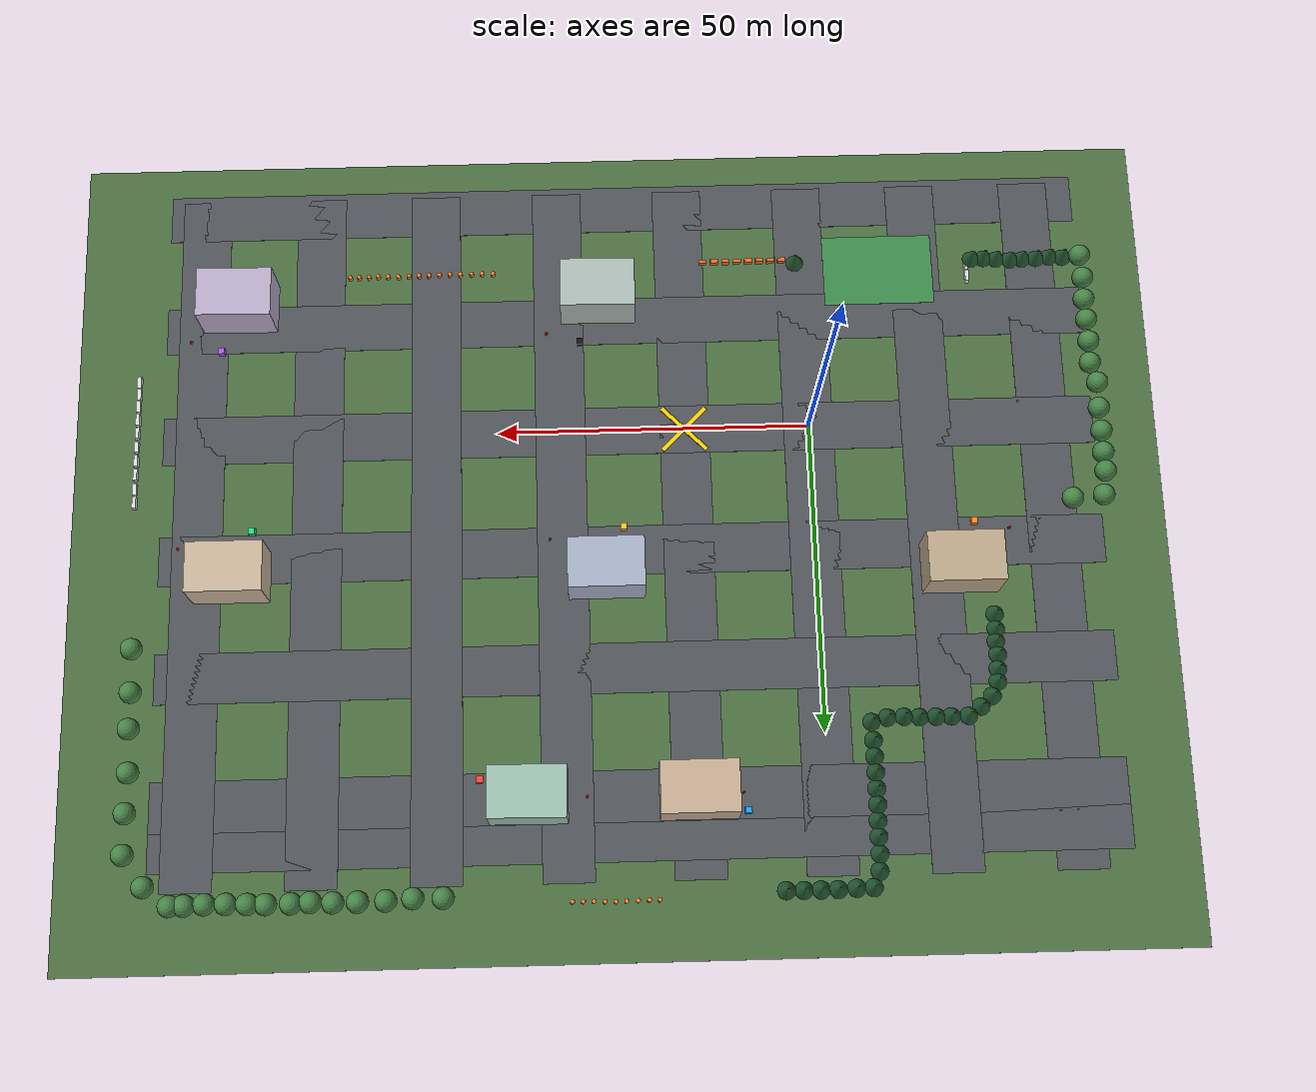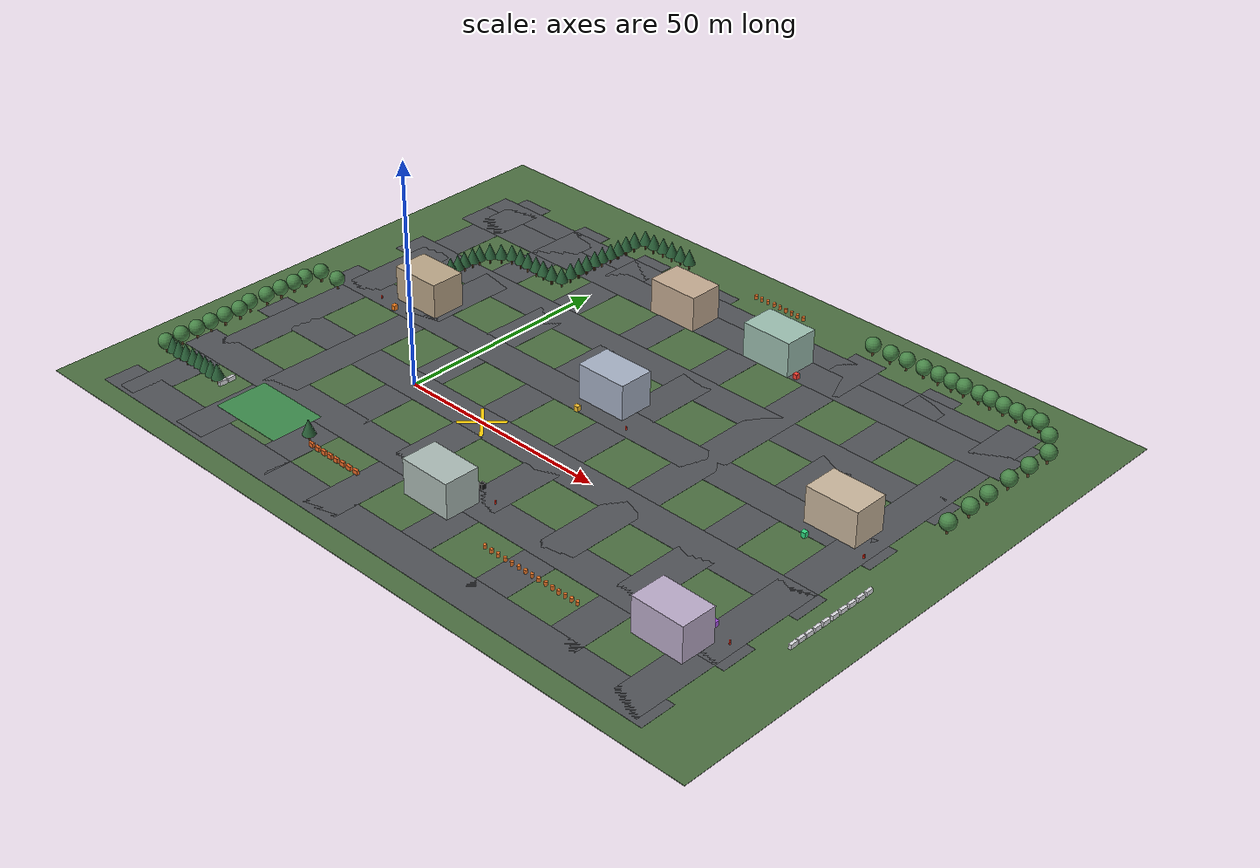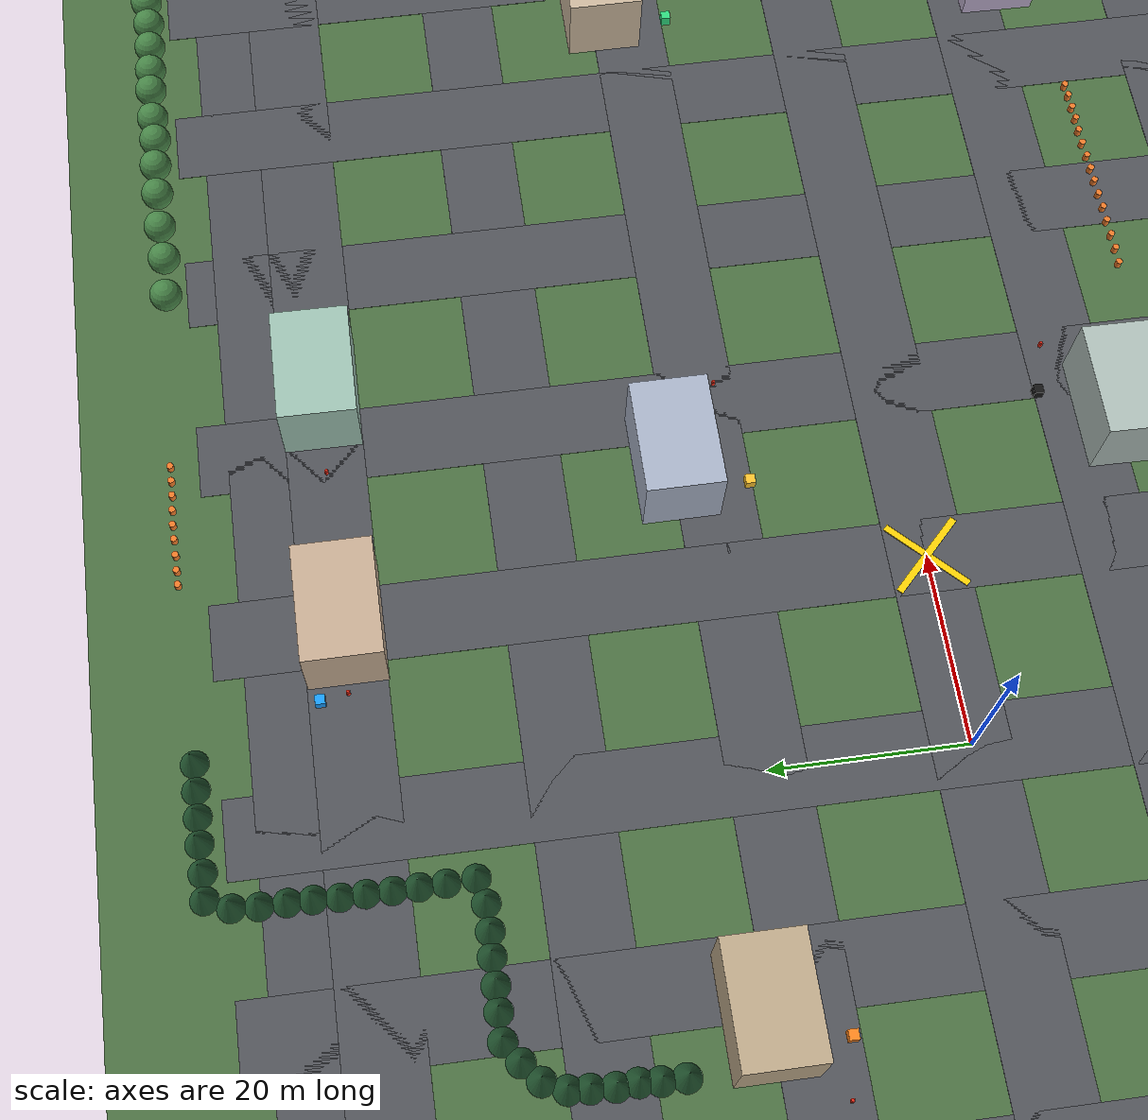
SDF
<sdf version="1.9">
 <world name="campus_pucrs">
  <gravity>0 0 -9.8</gravity>
  <physics name="default" type="dartsim">
   <max_step_size>0.01</max_step_size>
   <real_time_factor>1.0</real_time_factor>
  </physics>
  <plugin filename="gz-sim-physics-system" name="gz::sim::systems::Physics"/>
  <plugin filename="gz-sim-user-commands-system" name="gz::sim::systems::UserCommands"/>
  <plugin filename="gz-sim-scene-broadcaster-system" name="gz::sim::systems::SceneBroadcaster"/>
  <plugin filename="gz-sim-sensors-system" name="gz::sim::systems::Sensors">
   <render_engine>ogre2</render_engine>
  </plugin>
  <scene>
   <ambient>0.42 0.46 0.50 1</ambient>
   <background>0.05 0.08 0.12 1</background>
   <shadows>true</shadows>
  </scene>
  <light name="sun" type="directional">
   <pose>30 20 80 0 0 0</pose>
   <diffuse>0.9 0.92 0.95 1</diffuse>
   <specular>0.25 0.25 0.25 1</specular>
   <direction>-0.35 0.20 -0.90</direction>
  </light>
  <model name="campus_ground">
   <static>true</static>
   <link name="link">
    <collision name="ground_collision">
     <pose>31.0 18.0 -0.05 0 0 0.0</pose>
     <geometry><box><size>174.0 132.0 0.1</size></box></geometry>
     <surface><friction><ode><mu>1.0</mu><mu2>1.0</mu2></ode></friction></surface>
    </collision>
    <visual name="ground_visual">
     <pose>31.0 18.0 -0.05 0 0 0.0</pose>
     <geometry><box><size>174.0 132.0 0.1</size></box></geometry>
     <material><ambient>0.180 0.264 0.156 1</ambient><diffuse>0.3 0.44 0.26 1</diffuse></material>
    </visual>
   </link>
  </model>
  <model name="robot_spawn_marker_x">
   <static>true</static>
   <link name="link">
    <visual name="spawn_marker_arm_a_visual">
     <pose>20.0 0.0 0.090 0 0 0.785398</pose>
     <geometry><box><size>10.0 0.72 0.08</size></box></geometry>
     <material>
      <ambient>1.0 0.82 0.02 1</ambient>
      <diffuse>1.0 0.82 0.02 1</diffuse>
      <emissive>1.0 0.82 0.02 1</emissive>
     </material>
    </visual>
    <visual name="spawn_marker_arm_b_visual">
     <pose>20.0 0.0 0.093 0 0 -0.785398</pose>
     <geometry><box><size>10.0 0.72 0.08</size></box></geometry>
     <material>
      <ambient>1.0 0.82 0.02 1</ambient>
      <diffuse>1.0 0.82 0.02 1</diffuse>
      <emissive>1.0 0.82 0.02 1</emissive>
     </material>
    </visual>
   </link>
  </model>
  <model name="road_v_-38.0">
   <static>true</static>
   <link name="link">
    <visual name="road_visual">
     <pose>-38.0 15.0 0.02 0 0 0.0</pose>
     <geometry><box><size>8.0 114.0 0.04</size></box></geometry>
     <material><ambient>0.192 0.198 0.210 1</ambient><diffuse>0.32 0.33 0.35 1</diffuse></material>
    </visual>
   </link>
  </model>
  <model name="road_v_-19.0">
   <static>true</static>
   <link name="link">
    <visual name="road_visual">
     <pose>-19.0 15.0 0.02 0 0 0.0</pose>
     <geometry><box><size>8.0 114.0 0.04</size></box></geometry>
     <material><ambient>0.192 0.198 0.210 1</ambient><diffuse>0.32 0.33 0.35 1</diffuse></material>
    </visual>
   </link>
  </model>
  <model name="road_v_0.0">
   <static>true</static>
   <link name="link">
    <visual name="road_visual">
     <pose>0.0 15.0 0.02 0 0 0.0</pose>
     <geometry><box><size>8.0 114.0 0.04</size></box></geometry>
     <material><ambient>0.192 0.198 0.210 1</ambient><diffuse>0.32 0.33 0.35 1</diffuse></material>
    </visual>
   </link>
  </model>
  <model name="road_v_20.0">
   <static>true</static>
   <link name="link">
    <visual name="road_visual">
     <pose>20.0 15.0 0.02 0 0 0.0</pose>
     <geometry><box><size>8.0 114.0 0.04</size></box></geometry>
     <material><ambient>0.192 0.198 0.210 1</ambient><diffuse>0.32 0.33 0.35 1</diffuse></material>
    </visual>
   </link>
  </model>
  <model name="road_v_40.0">
   <static>true</static>
   <link name="link">
    <visual name="road_visual">
     <pose>40.0 15.0 0.02 0 0 0.0</pose>
     <geometry><box><size>8.0 114.0 0.04</size></box></geometry>
     <material><ambient>0.192 0.198 0.210 1</ambient><diffuse>0.32 0.33 0.35 1</diffuse></material>
    </visual>
   </link>
  </model>
  <model name="road_v_60.0">
   <static>true</static>
   <link name="link">
    <visual name="road_visual">
     <pose>60.0 15.0 0.02 0 0 0.0</pose>
     <geometry><box><size>8.0 114.0 0.04</size></box></geometry>
     <material><ambient>0.192 0.198 0.210 1</ambient><diffuse>0.32 0.33 0.35 1</diffuse></material>
    </visual>
   </link>
  </model>
  <model name="road_v_79.0">
   <static>true</static>
   <link name="link">
    <visual name="road_visual">
     <pose>79.0 15.0 0.02 0 0 0.0</pose>
     <geometry><box><size>8.0 114.0 0.04</size></box></geometry>
     <material><ambient>0.192 0.198 0.210 1</ambient><diffuse>0.32 0.33 0.35 1</diffuse></material>
    </visual>
   </link>
  </model>
  <model name="road_v_98.0">
   <static>true</static>
   <link name="link">
    <visual name="road_visual">
     <pose>98.0 15.0 0.02 0 0 0.0</pose>
     <geometry><box><size>8.0 114.0 0.04</size></box></geometry>
     <material><ambient>0.192 0.198 0.210 1</ambient><diffuse>0.32 0.33 0.35 1</diffuse></material>
    </visual>
   </link>
  </model>
  <model name="road_h_-39.0">
   <static>true</static>
   <link name="link">
    <visual name="road_visual">
     <pose>29.0 -39.0 0.02 0 0 0.0</pose>
     <geometry><box><size>150.0 8.0 0.04</size></box></geometry>
     <material><ambient>0.192 0.198 0.210 1</ambient><diffuse>0.32 0.33 0.35 1</diffuse></material>
    </visual>
   </link>
  </model>
  <model name="road_h_-19.0">
   <static>true</static>
   <link name="link">
    <visual name="road_visual">
     <pose>29.0 -19.0 0.02 0 0 0.0</pose>
     <geometry><box><size>150.0 8.0 0.04</size></box></geometry>
     <material><ambient>0.192 0.198 0.210 1</ambient><diffuse>0.32 0.33 0.35 1</diffuse></material>
    </visual>
   </link>
  </model>
  <model name="road_h_0.0">
   <static>true</static>
   <link name="link">
    <visual name="road_visual">
     <pose>29.0 0.0 0.02 0 0 0.0</pose>
     <geometry><box><size>150.0 8.0 0.04</size></box></geometry>
     <material><ambient>0.192 0.198 0.210 1</ambient><diffuse>0.32 0.33 0.35 1</diffuse></material>
    </visual>
   </link>
  </model>
  <model name="road_h_20.0">
   <static>true</static>
   <link name="link">
    <visual name="road_visual">
     <pose>29.0 20.0 0.02 0 0 0.0</pose>
     <geometry><box><size>150.0 8.0 0.04</size></box></geometry>
     <material><ambient>0.192 0.198 0.210 1</ambient><diffuse>0.32 0.33 0.35 1</diffuse></material>
    </visual>
   </link>
  </model>
  <model name="road_h_39.0">
   <static>true</static>
   <link name="link">
    <visual name="road_visual">
     <pose>29.0 39.0 0.02 0 0 0.0</pose>
     <geometry><box><size>150.0 8.0 0.04</size></box></geometry>
     <material><ambient>0.192 0.198 0.210 1</ambient><diffuse>0.32 0.33 0.35 1</diffuse></material>
    </visual>
   </link>
  </model>
  <model name="road_h_59.0">
   <static>true</static>
   <link name="link">
    <visual name="road_visual">
     <pose>29.0 59.0 0.02 0 0 0.0</pose>
     <geometry><box><size>150.0 8.0 0.04</size></box></geometry>
     <material><ambient>0.192 0.198 0.210 1</ambient><diffuse>0.32 0.33 0.35 1</diffuse></material>
    </visual>
   </link>
  </model>
  <model name="road_h_65.0">
   <static>true</static>
   <link name="link">
    <visual name="road_visual">
     <pose>29.0 65.0 0.02 0 0 0.0</pose>
     <geometry><box><size>150.0 8.0 0.04</size></box></geometry>
     <material><ambient>0.192 0.198 0.210 1</ambient><diffuse>0.32 0.33 0.35 1</diffuse></material>
    </visual>
   </link>
  </model>
  <model name="school_1">
   <static>true</static>
   <link name="link">
    <collision name="body_collision">
     <pose>-22.51 24.33 4.0 0 0 0.0</pose>
     <geometry><box><size>12 8 8</size></box></geometry>
    </collision>
    <visual name="body_visual">
     <pose>-22.51 24.33 4.0 0 0 0.0</pose>
     <geometry><box><size>12 8 8</size></box></geometry>
     <material><ambient>0.444 0.396 0.324 1</ambient><diffuse>0.74 0.66 0.54 1</diffuse></material>
    </visual>
   </link>
  </model>
  <model name="school_2">
   <static>true</static>
   <link name="link">
    <collision name="body_collision">
     <pose>33.17 23.81 4.0 0 0 0.0</pose>
     <geometry><box><size>12 8 8</size></box></geometry>
    </collision>
    <visual name="body_visual">
     <pose>33.17 23.81 4.0 0 0 0.0</pose>
     <geometry><box><size>12 8 8</size></box></geometry>
     <material><ambient>0.396 0.420 0.468 1</ambient><diffuse>0.66 0.7 0.78 1</diffuse></material>
    </visual>
   </link>
  </model>
  <model name="school_3">
   <static>true</static>
   <link name="link">
    <collision name="body_collision">
     <pose>92.17 23.02 4.0 0 0 0.0</pose>
     <geometry><box><size>12 8 8</size></box></geometry>
    </collision>
    <visual name="body_visual">
     <pose>92.17 23.02 4.0 0 0 0.0</pose>
     <geometry><box><size>12 8 8</size></box></geometry>
     <material><ambient>0.480 0.432 0.372 1</ambient><diffuse>0.8 0.72 0.62 1</diffuse></material>
    </visual>
   </link>
  </model>
  <model name="school_4">
   <static>true</static>
   <link name="link">
    <collision name="body_collision">
     <pose>45.89 58.97 4.0 0 0 1.56</pose>
     <geometry><box><size>8 12 8</size></box></geometry>
    </collision>
    <visual name="body_visual">
     <pose>45.89 58.97 4.0 0 0 1.56</pose>
     <geometry><box><size>8 12 8</size></box></geometry>
     <material><ambient>0.372 0.456 0.420 1</ambient><diffuse>0.62 0.76 0.7 1</diffuse></material>
    </visual>
   </link>
  </model>
  <model name="school_5">
   <static>true</static>
   <link name="link">
    <collision name="body_collision">
     <pose>91.89 -22.61 4.0 0 0 3.13</pose>
     <geometry><box><size>12 8 8</size></box></geometry>
    </collision>
    <visual name="body_visual">
     <pose>91.89 -22.61 4.0 0 0 3.13</pose>
     <geometry><box><size>12 8 8</size></box></geometry>
     <material><ambient>0.444 0.408 0.480 1</ambient><diffuse>0.74 0.68 0.8 1</diffuse></material>
    </visual>
   </link>
  </model>
  <model name="school_6">
   <static>true</static>
   <link name="link">
    <collision name="body_collision">
     <pose>33.47 -22.74 4.0 0 0 3.13</pose>
     <geometry><box><size>12 8 8</size></box></geometry>
    </collision>
    <visual name="body_visual">
     <pose>33.47 -22.74 4.0 0 0 3.13</pose>
     <geometry><box><size>12 8 8</size></box></geometry>
     <material><ambient>0.408 0.444 0.432 1</ambient><diffuse>0.68 0.74 0.72 1</diffuse></material>
    </visual>
   </link>
  </model>
  <model name="school_7">
   <static>true</static>
   <link name="link">
    <collision name="body_collision">
     <pose>19.96 58.89 4.0 0 0 -1.57</pose>
     <geometry><box><size>8 12 8</size></box></geometry>
    </collision>
    <visual name="body_visual">
     <pose>19.96 58.89 4.0 0 0 -1.57</pose>
     <geometry><box><size>8 12 8</size></box></geometry>
     <material><ambient>0.468 0.408 0.348 1</ambient><diffuse>0.78 0.68 0.58 1</diffuse></material>
    </visual>
   </link>
  </model>
  <model name="robocup_field">
   <static>true</static>
   <link name="link">
    <visual name="field_visual">
     <pose>-12.92 -26.97 0.03 0 0 0.0</pose>
     <geometry><box><size>18.0 12.0 0.06</size></box></geometry>
     <material><ambient>0.144 0.330 0.180 1</ambient><diffuse>0.24 0.55 0.3 1</diffuse></material>
    </visual>
   </link>
  </model>
  <model name="oak_tree_0">
   <static>true</static>
   <link name="link">
    <collision name="trunk_collision">
     <pose>-45.8507 -27.6084 0.8 0.0 0.0 0</pose>
     <geometry><cylinder><radius>0.25</radius><length>1.6</length></cylinder></geometry>
    </collision>
    <visual name="trunk_visual">
     <pose>-45.8507 -27.6084 0.8 0.0 0.0 0</pose>
     <geometry><cylinder><radius>0.25</radius><length>1.6</length></cylinder></geometry>
     <material><ambient>0.252 0.180 0.108 1</ambient><diffuse>0.42 0.3 0.18 1</diffuse></material>
    </visual>
    <visual name="crown_visual">
     <pose>-45.8507 -27.6084 2.6 0 0 0</pose>
     <geometry><sphere><radius>1.7</radius></sphere></geometry>
     <material><ambient>0.168 0.312 0.168 1</ambient><diffuse>0.28 0.52 0.28 1</diffuse></material>
    </visual>
   </link>
  </model>
  <model name="oak_tree_1">
   <static>true</static>
   <link name="link">
    <collision name="trunk_collision">
     <pose>58.7873 73.9068 0.8 0.0 0.0 0</pose>
     <geometry><cylinder><radius>0.25</radius><length>1.6</length></cylinder></geometry>
    </collision>
    <visual name="trunk_visual">
     <pose>58.7873 73.9068 0.8 0.0 0.0 0</pose>
     <geometry><cylinder><radius>0.25</radius><length>1.6</length></cylinder></geometry>
     <material><ambient>0.252 0.180 0.108 1</ambient><diffuse>0.42 0.3 0.18 1</diffuse></material>
    </visual>
    <visual name="crown_visual">
     <pose>58.7873 73.9068 2.6 0 0 0</pose>
     <geometry><sphere><radius>1.7</radius></sphere></geometry>
     <material><ambient>0.168 0.312 0.168 1</ambient><diffuse>0.28 0.52 0.28 1</diffuse></material>
    </visual>
   </link>
  </model>
  <model name="oak_tree_2">
   <static>true</static>
   <link name="link">
    <collision name="trunk_collision">
     <pose>63.3588 73.8542 0.8 0.0 0.0 0</pose>
     <geometry><cylinder><radius>0.25</radius><length>1.6</length></cylinder></geometry>
    </collision>
    <visual name="trunk_visual">
     <pose>63.3588 73.8542 0.8 0.0 0.0 0</pose>
     <geometry><cylinder><radius>0.25</radius><length>1.6</length></cylinder></geometry>
     <material><ambient>0.252 0.180 0.108 1</ambient><diffuse>0.42 0.3 0.18 1</diffuse></material>
    </visual>
    <visual name="crown_visual">
     <pose>63.3588 73.8542 2.6 0 0 0</pose>
     <geometry><sphere><radius>1.7</radius></sphere></geometry>
     <material><ambient>0.168 0.312 0.168 1</ambient><diffuse>0.28 0.52 0.28 1</diffuse></material>
    </visual>
   </link>
  </model>
  <model name="oak_tree_3">
   <static>true</static>
   <link name="link">
    <collision name="trunk_collision">
     <pose>67.3848 74.0914 0.8 0.0 0.0 0</pose>
     <geometry><cylinder><radius>0.25</radius><length>1.6</length></cylinder></geometry>
    </collision>
    <visual name="trunk_visual">
     <pose>67.3848 74.0914 0.8 0.0 0.0 0</pose>
     <geometry><cylinder><radius>0.25</radius><length>1.6</length></cylinder></geometry>
     <material><ambient>0.252 0.180 0.108 1</ambient><diffuse>0.42 0.3 0.18 1</diffuse></material>
    </visual>
    <visual name="crown_visual">
     <pose>67.3848 74.0914 2.6 0 0 0</pose>
     <geometry><sphere><radius>1.7</radius></sphere></geometry>
     <material><ambient>0.168 0.312 0.168 1</ambient><diffuse>0.28 0.52 0.28 1</diffuse></material>
    </visual>
   </link>
  </model>
  <model name="oak_tree_4">
   <static>true</static>
   <link name="link">
    <collision name="trunk_collision">
     <pose>71.6046 74.1445 0.8 0.0 0.0 0</pose>
     <geometry><cylinder><radius>0.25</radius><length>1.6</length></cylinder></geometry>
    </collision>
    <visual name="trunk_visual">
     <pose>71.6046 74.1445 0.8 0.0 0.0 0</pose>
     <geometry><cylinder><radius>0.25</radius><length>1.6</length></cylinder></geometry>
     <material><ambient>0.252 0.180 0.108 1</ambient><diffuse>0.42 0.3 0.18 1</diffuse></material>
    </visual>
    <visual name="crown_visual">
     <pose>71.6046 74.1445 2.6 0 0 0</pose>
     <geometry><sphere><radius>1.7</radius></sphere></geometry>
     <material><ambient>0.168 0.312 0.168 1</ambient><diffuse>0.28 0.52 0.28 1</diffuse></material>
    </visual>
   </link>
  </model>
  <model name="oak_tree_5">
   <static>true</static>
   <link name="link">
    <collision name="trunk_collision">
     <pose>99.8071 74.0512 0.8 0.0 0.0 0</pose>
     <geometry><cylinder><radius>0.25</radius><length>1.6</length></cylinder></geometry>
    </collision>
    <visual name="trunk_visual">
     <pose>99.8071 74.0512 0.8 0.0 0.0 0</pose>
     <geometry><cylinder><radius>0.25</radius><length>1.6</length></cylinder></geometry>
     <material><ambient>0.252 0.180 0.108 1</ambient><diffuse>0.42 0.3 0.18 1</diffuse></material>
    </visual>
    <visual name="crown_visual">
     <pose>99.8071 74.0512 2.6 0 0 0</pose>
     <geometry><sphere><radius>1.7</radius></sphere></geometry>
     <material><ambient>0.168 0.312 0.168 1</ambient><diffuse>0.28 0.52 0.28 1</diffuse></material>
    </visual>
   </link>
  </model>
  <model name="oak_tree_6">
   <static>true</static>
   <link name="link">
    <collision name="trunk_collision">
     <pose>103.833 71.1472 0.8 0.0 0.0 0</pose>
     <geometry><cylinder><radius>0.25</radius><length>1.6</length></cylinder></geometry>
    </collision>
    <visual name="trunk_visual">
     <pose>103.833 71.1472 0.8 0.0 0.0 0</pose>
     <geometry><cylinder><radius>0.25</radius><length>1.6</length></cylinder></geometry>
     <material><ambient>0.252 0.180 0.108 1</ambient><diffuse>0.42 0.3 0.18 1</diffuse></material>
    </visual>
    <visual name="crown_visual">
     <pose>103.833 71.1472 2.6 0 0 0</pose>
     <geometry><sphere><radius>1.7</radius></sphere></geometry>
     <material><ambient>0.168 0.312 0.168 1</ambient><diffuse>0.28 0.52 0.28 1</diffuse></material>
    </visual>
   </link>
  </model>
  <model name="oak_tree_7">
   <static>true</static>
   <link name="link">
    <collision name="trunk_collision">
     <pose>107.085 66.2785 0.8 0.0 0.0 0</pose>
     <geometry><cylinder><radius>0.25</radius><length>1.6</length></cylinder></geometry>
    </collision>
    <visual name="trunk_visual">
     <pose>107.085 66.2785 0.8 0.0 0.0 0</pose>
     <geometry><cylinder><radius>0.25</radius><length>1.6</length></cylinder></geometry>
     <material><ambient>0.252 0.180 0.108 1</ambient><diffuse>0.42 0.3 0.18 1</diffuse></material>
    </visual>
    <visual name="crown_visual">
     <pose>107.085 66.2785 2.6 0 0 0</pose>
     <geometry><sphere><radius>1.7</radius></sphere></geometry>
     <material><ambient>0.168 0.312 0.168 1</ambient><diffuse>0.28 0.52 0.28 1</diffuse></material>
    </visual>
   </link>
  </model>
  <model name="oak_tree_8">
   <static>true</static>
   <link name="link">
    <collision name="trunk_collision">
     <pose>107.0 60.0 0.8 0.0 0.0 0</pose>
     <geometry><cylinder><radius>0.25</radius><length>1.6</length></cylinder></geometry>
    </collision>
    <visual name="trunk_visual">
     <pose>107.0 60.0 0.8 0.0 0.0 0</pose>
     <geometry><cylinder><radius>0.25</radius><length>1.6</length></cylinder></geometry>
     <material><ambient>0.252 0.180 0.108 1</ambient><diffuse>0.42 0.3 0.18 1</diffuse></material>
    </visual>
    <visual name="crown_visual">
     <pose>107.0 60.0 2.6 0 0 0</pose>
     <geometry><sphere><radius>1.7</radius></sphere></geometry>
     <material><ambient>0.168 0.312 0.168 1</ambient><diffuse>0.28 0.52 0.28 1</diffuse></material>
    </visual>
   </link>
  </model>
  <model name="oak_tree_9">
   <static>true</static>
   <link name="link">
    <collision name="trunk_collision">
     <pose>106.778 53.8309 0.8 0.0 0.0 0</pose>
     <geometry><cylinder><radius>0.25</radius><length>1.6</length></cylinder></geometry>
    </collision>
    <visual name="trunk_visual">
     <pose>106.778 53.8309 0.8 0.0 0.0 0</pose>
     <geometry><cylinder><radius>0.25</radius><length>1.6</length></cylinder></geometry>
     <material><ambient>0.252 0.180 0.108 1</ambient><diffuse>0.42 0.3 0.18 1</diffuse></material>
    </visual>
    <visual name="crown_visual">
     <pose>106.778 53.8309 2.6 0 0 0</pose>
     <geometry><sphere><radius>1.7</radius></sphere></geometry>
     <material><ambient>0.168 0.312 0.168 1</ambient><diffuse>0.28 0.52 0.28 1</diffuse></material>
    </visual>
   </link>
  </model>
  <model name="oak_tree_10">
   <static>true</static>
   <link name="link">
    <collision name="trunk_collision">
     <pose>106.957 47.0737 0.8 0.0 0.0 0</pose>
     <geometry><cylinder><radius>0.25</radius><length>1.6</length></cylinder></geometry>
    </collision>
    <visual name="trunk_visual">
     <pose>106.957 47.0737 0.8 0.0 0.0 0</pose>
     <geometry><cylinder><radius>0.25</radius><length>1.6</length></cylinder></geometry>
     <material><ambient>0.252 0.180 0.108 1</ambient><diffuse>0.42 0.3 0.18 1</diffuse></material>
    </visual>
    <visual name="crown_visual">
     <pose>106.957 47.0737 2.6 0 0 0</pose>
     <geometry><sphere><radius>1.7</radius></sphere></geometry>
     <material><ambient>0.168 0.312 0.168 1</ambient><diffuse>0.28 0.52 0.28 1</diffuse></material>
    </visual>
   </link>
  </model>
  <model name="oak_tree_11">
   <static>true</static>
   <link name="link">
    <collision name="trunk_collision">
     <pose>106.932 41.4 0.8 0.0 0.0 0</pose>
     <geometry><cylinder><radius>0.25</radius><length>1.6</length></cylinder></geometry>
    </collision>
    <visual name="trunk_visual">
     <pose>106.932 41.4 0.8 0.0 0.0 0</pose>
     <geometry><cylinder><radius>0.25</radius><length>1.6</length></cylinder></geometry>
     <material><ambient>0.252 0.180 0.108 1</ambient><diffuse>0.42 0.3 0.18 1</diffuse></material>
    </visual>
    <visual name="crown_visual">
     <pose>106.932 41.4 2.6 0 0 0</pose>
     <geometry><sphere><radius>1.7</radius></sphere></geometry>
     <material><ambient>0.168 0.312 0.168 1</ambient><diffuse>0.28 0.52 0.28 1</diffuse></material>
    </visual>
   </link>
  </model>
  <model name="oak_tree_12">
   <static>true</static>
   <link name="link">
    <collision name="trunk_collision">
     <pose>107.049 34.5471 0.8 0.0 0.0 0</pose>
     <geometry><cylinder><radius>0.25</radius><length>1.6</length></cylinder></geometry>
    </collision>
    <visual name="trunk_visual">
     <pose>107.049 34.5471 0.8 0.0 0.0 0</pose>
     <geometry><cylinder><radius>0.25</radius><length>1.6</length></cylinder></geometry>
     <material><ambient>0.252 0.180 0.108 1</ambient><diffuse>0.42 0.3 0.18 1</diffuse></material>
    </visual>
    <visual name="crown_visual">
     <pose>107.049 34.5471 2.6 0 0 0</pose>
     <geometry><sphere><radius>1.7</radius></sphere></geometry>
     <material><ambient>0.168 0.312 0.168 1</ambient><diffuse>0.28 0.52 0.28 1</diffuse></material>
    </visual>
   </link>
  </model>
  <model name="oak_tree_13">
   <static>true</static>
   <link name="link">
    <collision name="trunk_collision">
     <pose>75.2969 74.1503 0.8 0.0 0.0 0</pose>
     <geometry><cylinder><radius>0.25</radius><length>1.6</length></cylinder></geometry>
    </collision>
    <visual name="trunk_visual">
     <pose>75.2969 74.1503 0.8 0.0 0.0 0</pose>
     <geometry><cylinder><radius>0.25</radius><length>1.6</length></cylinder></geometry>
     <material><ambient>0.252 0.180 0.108 1</ambient><diffuse>0.42 0.3 0.18 1</diffuse></material>
    </visual>
    <visual name="crown_visual">
     <pose>75.2969 74.1503 2.6 0 0 0</pose>
     <geometry><sphere><radius>1.7</radius></sphere></geometry>
     <material><ambient>0.168 0.312 0.168 1</ambient><diffuse>0.28 0.52 0.28 1</diffuse></material>
    </visual>
   </link>
  </model>
  <model name="oak_tree_14">
   <static>true</static>
   <link name="link">
    <collision name="trunk_collision">
     <pose>78.6553 74.017 0.8 0.0 0.0 0</pose>
     <geometry><cylinder><radius>0.25</radius><length>1.6</length></cylinder></geometry>
    </collision>
    <visual name="trunk_visual">
     <pose>78.6553 74.017 0.8 0.0 0.0 0</pose>
     <geometry><cylinder><radius>0.25</radius><length>1.6</length></cylinder></geometry>
     <material><ambient>0.252 0.180 0.108 1</ambient><diffuse>0.42 0.3 0.18 1</diffuse></material>
    </visual>
    <visual name="crown_visual">
     <pose>78.6553 74.017 2.6 0 0 0</pose>
     <geometry><sphere><radius>1.7</radius></sphere></geometry>
     <material><ambient>0.168 0.312 0.168 1</ambient><diffuse>0.28 0.52 0.28 1</diffuse></material>
    </visual>
   </link>
  </model>
  <model name="oak_tree_15">
   <static>true</static>
   <link name="link">
    <collision name="trunk_collision">
     <pose>81.5914 74.1371 0.8 0.0 0.0 0</pose>
     <geometry><cylinder><radius>0.25</radius><length>1.6</length></cylinder></geometry>
    </collision>
    <visual name="trunk_visual">
     <pose>81.5914 74.1371 0.8 0.0 0.0 0</pose>
     <geometry><cylinder><radius>0.25</radius><length>1.6</length></cylinder></geometry>
     <material><ambient>0.252 0.180 0.108 1</ambient><diffuse>0.42 0.3 0.18 1</diffuse></material>
    </visual>
    <visual name="crown_visual">
     <pose>81.5914 74.1371 2.6 0 0 0</pose>
     <geometry><sphere><radius>1.7</radius></sphere></geometry>
     <material><ambient>0.168 0.312 0.168 1</ambient><diffuse>0.28 0.52 0.28 1</diffuse></material>
    </visual>
   </link>
  </model>
  <model name="oak_tree_16">
   <static>true</static>
   <link name="link">
    <collision name="trunk_collision">
     <pose>85.3365 74.1434 0.8 0.0 0.0 0</pose>
     <geometry><cylinder><radius>0.25</radius><length>1.6</length></cylinder></geometry>
    </collision>
    <visual name="trunk_visual">
     <pose>85.3365 74.1434 0.8 0.0 0.0 0</pose>
     <geometry><cylinder><radius>0.25</radius><length>1.6</length></cylinder></geometry>
     <material><ambient>0.252 0.180 0.108 1</ambient><diffuse>0.42 0.3 0.18 1</diffuse></material>
    </visual>
    <visual name="crown_visual">
     <pose>85.3365 74.1434 2.6 0 0 0</pose>
     <geometry><sphere><radius>1.7</radius></sphere></geometry>
     <material><ambient>0.168 0.312 0.168 1</ambient><diffuse>0.28 0.52 0.28 1</diffuse></material>
    </visual>
   </link>
  </model>
  <model name="oak_tree_17">
   <static>true</static>
   <link name="link">
    <collision name="trunk_collision">
     <pose>88.1147 74.0554 0.8 0.0 0.0 0</pose>
     <geometry><cylinder><radius>0.25</radius><length>1.6</length></cylinder></geometry>
    </collision>
    <visual name="trunk_visual">
     <pose>88.1147 74.0554 0.8 0.0 0.0 0</pose>
     <geometry><cylinder><radius>0.25</radius><length>1.6</length></cylinder></geometry>
     <material><ambient>0.252 0.180 0.108 1</ambient><diffuse>0.42 0.3 0.18 1</diffuse></material>
    </visual>
    <visual name="crown_visual">
     <pose>88.1147 74.0554 2.6 0 0 0</pose>
     <geometry><sphere><radius>1.7</radius></sphere></geometry>
     <material><ambient>0.168 0.312 0.168 1</ambient><diffuse>0.28 0.52 0.28 1</diffuse></material>
    </visual>
   </link>
  </model>
  <model name="oak_tree_18">
   <static>true</static>
   <link name="link">
    <collision name="trunk_collision">
     <pose>91.2972 73.9451 0.8 0.0 0.0 0</pose>
     <geometry><cylinder><radius>0.25</radius><length>1.6</length></cylinder></geometry>
    </collision>
    <visual name="trunk_visual">
     <pose>91.2972 73.9451 0.8 0.0 0.0 0</pose>
     <geometry><cylinder><radius>0.25</radius><length>1.6</length></cylinder></geometry>
     <material><ambient>0.252 0.180 0.108 1</ambient><diffuse>0.42 0.3 0.18 1</diffuse></material>
    </visual>
    <visual name="crown_visual">
     <pose>91.2972 73.9451 2.6 0 0 0</pose>
     <geometry><sphere><radius>1.7</radius></sphere></geometry>
     <material><ambient>0.168 0.312 0.168 1</ambient><diffuse>0.28 0.52 0.28 1</diffuse></material>
    </visual>
   </link>
  </model>
  <model name="oak_tree_19">
   <static>true</static>
   <link name="link">
    <collision name="trunk_collision">
     <pose>94.4973 73.927 0.8 0.0 0.0 0</pose>
     <geometry><cylinder><radius>0.25</radius><length>1.6</length></cylinder></geometry>
    </collision>
    <visual name="trunk_visual">
     <pose>94.4973 73.927 0.8 0.0 0.0 0</pose>
     <geometry><cylinder><radius>0.25</radius><length>1.6</length></cylinder></geometry>
     <material><ambient>0.252 0.180 0.108 1</ambient><diffuse>0.42 0.3 0.18 1</diffuse></material>
    </visual>
    <visual name="crown_visual">
     <pose>94.4973 73.927 2.6 0 0 0</pose>
     <geometry><sphere><radius>1.7</radius></sphere></geometry>
     <material><ambient>0.168 0.312 0.168 1</ambient><diffuse>0.28 0.52 0.28 1</diffuse></material>
    </visual>
   </link>
  </model>
  <model name="oak_tree_20">
   <static>true</static>
   <link name="link">
    <collision name="trunk_collision">
     <pose>97.5564 74.0473 0.8 0.0 0.0 0</pose>
     <geometry><cylinder><radius>0.25</radius><length>1.6</length></cylinder></geometry>
    </collision>
    <visual name="trunk_visual">
     <pose>97.5564 74.0473 0.8 0.0 0.0 0</pose>
     <geometry><cylinder><radius>0.25</radius><length>1.6</length></cylinder></geometry>
     <material><ambient>0.252 0.180 0.108 1</ambient><diffuse>0.42 0.3 0.18 1</diffuse></material>
    </visual>
    <visual name="crown_visual">
     <pose>97.5564 74.0473 2.6 0 0 0</pose>
     <geometry><sphere><radius>1.7</radius></sphere></geometry>
     <material><ambient>0.168 0.312 0.168 1</ambient><diffuse>0.28 0.52 0.28 1</diffuse></material>
    </visual>
   </link>
  </model>
  <model name="oak_tree_21">
   <static>true</static>
   <link name="link">
    <collision name="trunk_collision">
     <pose>-46.0054 -23.6481 0.8 0.0 0.0 0</pose>
     <geometry><cylinder><radius>0.25</radius><length>1.6</length></cylinder></geometry>
    </collision>
    <visual name="trunk_visual">
     <pose>-46.0054 -23.6481 0.8 0.0 0.0 0</pose>
     <geometry><cylinder><radius>0.25</radius><length>1.6</length></cylinder></geometry>
     <material><ambient>0.252 0.180 0.108 1</ambient><diffuse>0.42 0.3 0.18 1</diffuse></material>
    </visual>
    <visual name="crown_visual">
     <pose>-46.0054 -23.6481 2.6 0 0 0</pose>
     <geometry><sphere><radius>1.7</radius></sphere></geometry>
     <material><ambient>0.168 0.312 0.168 1</ambient><diffuse>0.28 0.52 0.28 1</diffuse></material>
    </visual>
   </link>
  </model>
  <model name="oak_tree_22">
   <static>true</static>
   <link name="link">
    <collision name="trunk_collision">
     <pose>-45.853 -19.83 0.8 0.0 0.0 0</pose>
     <geometry><cylinder><radius>0.25</radius><length>1.6</length></cylinder></geometry>
    </collision>
    <visual name="trunk_visual">
     <pose>-45.853 -19.83 0.8 0.0 0.0 0</pose>
     <geometry><cylinder><radius>0.25</radius><length>1.6</length></cylinder></geometry>
     <material><ambient>0.252 0.180 0.108 1</ambient><diffuse>0.42 0.3 0.18 1</diffuse></material>
    </visual>
    <visual name="crown_visual">
     <pose>-45.853 -19.83 2.6 0 0 0</pose>
     <geometry><sphere><radius>1.7</radius></sphere></geometry>
     <material><ambient>0.168 0.312 0.168 1</ambient><diffuse>0.28 0.52 0.28 1</diffuse></material>
    </visual>
   </link>
  </model>
  <model name="oak_tree_23">
   <static>true</static>
   <link name="link">
    <collision name="trunk_collision">
     <pose>-45.9444 -16.2895 0.8 0.0 0.0 0</pose>
     <geometry><cylinder><radius>0.25</radius><length>1.6</length></cylinder></geometry>
    </collision>
    <visual name="trunk_visual">
     <pose>-45.9444 -16.2895 0.8 0.0 0.0 0</pose>
     <geometry><cylinder><radius>0.25</radius><length>1.6</length></cylinder></geometry>
     <material><ambient>0.252 0.180 0.108 1</ambient><diffuse>0.42 0.3 0.18 1</diffuse></material>
    </visual>
    <visual name="crown_visual">
     <pose>-45.9444 -16.2895 2.6 0 0 0</pose>
     <geometry><sphere><radius>1.7</radius></sphere></geometry>
     <material><ambient>0.168 0.312 0.168 1</ambient><diffuse>0.28 0.52 0.28 1</diffuse></material>
    </visual>
   </link>
  </model>
  <model name="oak_tree_24">
   <static>true</static>
   <link name="link">
    <collision name="trunk_collision">
     <pose>-45.9615 -12.5098 0.8 0.0 0.0 0</pose>
     <geometry><cylinder><radius>0.25</radius><length>1.6</length></cylinder></geometry>
    </collision>
    <visual name="trunk_visual">
     <pose>-45.9615 -12.5098 0.8 0.0 0.0 0</pose>
     <geometry><cylinder><radius>0.25</radius><length>1.6</length></cylinder></geometry>
     <material><ambient>0.252 0.180 0.108 1</ambient><diffuse>0.42 0.3 0.18 1</diffuse></material>
    </visual>
    <visual name="crown_visual">
     <pose>-45.9615 -12.5098 2.6 0 0 0</pose>
     <geometry><sphere><radius>1.7</radius></sphere></geometry>
     <material><ambient>0.168 0.312 0.168 1</ambient><diffuse>0.28 0.52 0.28 1</diffuse></material>
    </visual>
   </link>
  </model>
  <model name="oak_tree_25">
   <static>true</static>
   <link name="link">
    <collision name="trunk_collision">
     <pose>-45.8262 -8.78087 0.8 0.0 0.0 0</pose>
     <geometry><cylinder><radius>0.25</radius><length>1.6</length></cylinder></geometry>
    </collision>
    <visual name="trunk_visual">
     <pose>-45.8262 -8.78087 0.8 0.0 0.0 0</pose>
     <geometry><cylinder><radius>0.25</radius><length>1.6</length></cylinder></geometry>
     <material><ambient>0.252 0.180 0.108 1</ambient><diffuse>0.42 0.3 0.18 1</diffuse></material>
    </visual>
    <visual name="crown_visual">
     <pose>-45.8262 -8.78087 2.6 0 0 0</pose>
     <geometry><sphere><radius>1.7</radius></sphere></geometry>
     <material><ambient>0.168 0.312 0.168 1</ambient><diffuse>0.28 0.52 0.28 1</diffuse></material>
    </visual>
   </link>
  </model>
  <model name="oak_tree_26">
   <static>true</static>
   <link name="link">
    <collision name="trunk_collision">
     <pose>-46.7063 -5.35408 0.8 0.0 0.0 0</pose>
     <geometry><cylinder><radius>0.25</radius><length>1.6</length></cylinder></geometry>
    </collision>
    <visual name="trunk_visual">
     <pose>-46.7063 -5.35408 0.8 0.0 0.0 0</pose>
     <geometry><cylinder><radius>0.25</radius><length>1.6</length></cylinder></geometry>
     <material><ambient>0.252 0.180 0.108 1</ambient><diffuse>0.42 0.3 0.18 1</diffuse></material>
    </visual>
    <visual name="crown_visual">
     <pose>-46.7063 -5.35408 2.6 0 0 0</pose>
     <geometry><sphere><radius>1.7</radius></sphere></geometry>
     <material><ambient>0.168 0.312 0.168 1</ambient><diffuse>0.28 0.52 0.28 1</diffuse></material>
    </visual>
   </link>
  </model>
  <model name="oak_tree_27">
   <static>true</static>
   <link name="link">
    <collision name="trunk_collision">
     <pose>-46.5387 -1.00848 0.8 0.0 0.0 0</pose>
     <geometry><cylinder><radius>0.25</radius><length>1.6</length></cylinder></geometry>
    </collision>
    <visual name="trunk_visual">
     <pose>-46.5387 -1.00848 0.8 0.0 0.0 0</pose>
     <geometry><cylinder><radius>0.25</radius><length>1.6</length></cylinder></geometry>
     <material><ambient>0.252 0.180 0.108 1</ambient><diffuse>0.42 0.3 0.18 1</diffuse></material>
    </visual>
    <visual name="crown_visual">
     <pose>-46.5387 -1.00848 2.6 0 0 0</pose>
     <geometry><sphere><radius>1.7</radius></sphere></geometry>
     <material><ambient>0.168 0.312 0.168 1</ambient><diffuse>0.28 0.52 0.28 1</diffuse></material>
    </visual>
   </link>
  </model>
  <model name="oak_tree_28">
   <static>true</static>
   <link name="link">
    <collision name="trunk_collision">
     <pose>-46.5984 2.87375 0.8 0.0 0.0 0</pose>
     <geometry><cylinder><radius>0.25</radius><length>1.6</length></cylinder></geometry>
    </collision>
    <visual name="trunk_visual">
     <pose>-46.5984 2.87375 0.8 0.0 0.0 0</pose>
     <geometry><cylinder><radius>0.25</radius><length>1.6</length></cylinder></geometry>
     <material><ambient>0.252 0.180 0.108 1</ambient><diffuse>0.42 0.3 0.18 1</diffuse></material>
    </visual>
    <visual name="crown_visual">
     <pose>-46.5984 2.87375 2.6 0 0 0</pose>
     <geometry><sphere><radius>1.7</radius></sphere></geometry>
     <material><ambient>0.168 0.312 0.168 1</ambient><diffuse>0.28 0.52 0.28 1</diffuse></material>
    </visual>
   </link>
  </model>
  <model name="oak_tree_29">
   <static>true</static>
   <link name="link">
    <collision name="trunk_collision">
     <pose>-46.5377 6.48958 0.8 0.0 0.0 0</pose>
     <geometry><cylinder><radius>0.25</radius><length>1.6</length></cylinder></geometry>
    </collision>
    <visual name="trunk_visual">
     <pose>-46.5377 6.48958 0.8 0.0 0.0 0</pose>
     <geometry><cylinder><radius>0.25</radius><length>1.6</length></cylinder></geometry>
     <material><ambient>0.252 0.180 0.108 1</ambient><diffuse>0.42 0.3 0.18 1</diffuse></material>
    </visual>
    <visual name="crown_visual">
     <pose>-46.5377 6.48958 2.6 0 0 0</pose>
     <geometry><sphere><radius>1.7</radius></sphere></geometry>
     <material><ambient>0.168 0.312 0.168 1</ambient><diffuse>0.28 0.52 0.28 1</diffuse></material>
    </visual>
   </link>
  </model>
  <model name="oak_tree_30">
   <static>true</static>
   <link name="link">
    <collision name="trunk_collision">
     <pose>-46.6255 9.61611 0.8 0.0 0.0 0</pose>
     <geometry><cylinder><radius>0.25</radius><length>1.6</length></cylinder></geometry>
    </collision>
    <visual name="trunk_visual">
     <pose>-46.6255 9.61611 0.8 0.0 0.0 0</pose>
     <geometry><cylinder><radius>0.25</radius><length>1.6</length></cylinder></geometry>
     <material><ambient>0.252 0.180 0.108 1</ambient><diffuse>0.42 0.3 0.18 1</diffuse></material>
    </visual>
    <visual name="crown_visual">
     <pose>-46.6255 9.61611 2.6 0 0 0</pose>
     <geometry><sphere><radius>1.7</radius></sphere></geometry>
     <material><ambient>0.168 0.312 0.168 1</ambient><diffuse>0.28 0.52 0.28 1</diffuse></material>
    </visual>
   </link>
  </model>
  <model name="oak_tree_31">
   <static>true</static>
   <link name="link">
    <collision name="trunk_collision">
     <pose>-46.0 13.5661 0.8 0.0 0.0 0</pose>
     <geometry><cylinder><radius>0.25</radius><length>1.6</length></cylinder></geometry>
    </collision>
    <visual name="trunk_visual">
     <pose>-46.0 13.5661 0.8 0.0 0.0 0</pose>
     <geometry><cylinder><radius>0.25</radius><length>1.6</length></cylinder></geometry>
     <material><ambient>0.252 0.180 0.108 1</ambient><diffuse>0.42 0.3 0.18 1</diffuse></material>
    </visual>
    <visual name="crown_visual">
     <pose>-46.0 13.5661 2.6 0 0 0</pose>
     <geometry><sphere><radius>1.7</radius></sphere></geometry>
     <material><ambient>0.168 0.312 0.168 1</ambient><diffuse>0.28 0.52 0.28 1</diffuse></material>
    </visual>
   </link>
  </model>
  <model name="oak_tree_32">
   <static>true</static>
   <link name="link">
    <collision name="trunk_collision">
     <pose>-41.0 14.0 0.8 0.0 0.0 0</pose>
     <geometry><cylinder><radius>0.25</radius><length>1.6</length></cylinder></geometry>
    </collision>
    <visual name="trunk_visual">
     <pose>-41.0 14.0 0.8 0.0 0.0 0</pose>
     <geometry><cylinder><radius>0.25</radius><length>1.6</length></cylinder></geometry>
     <material><ambient>0.252 0.180 0.108 1</ambient><diffuse>0.42 0.3 0.18 1</diffuse></material>
    </visual>
    <visual name="crown_visual">
     <pose>-41.0 14.0 2.6 0 0 0</pose>
     <geometry><sphere><radius>1.7</radius></sphere></geometry>
     <material><ambient>0.168 0.312 0.168 1</ambient><diffuse>0.28 0.52 0.28 1</diffuse></material>
    </visual>
   </link>
  </model>
  <model name="pine_tree_0">
   <static>true</static>
   <link name="link">
    <collision name="trunk_collision">
     <pose>-43.1953 -27.683 0.95 0.0 0.0 0</pose>
     <geometry><cylinder><radius>0.22</radius><length>1.9</length></cylinder></geometry>
    </collision>
    <visual name="trunk_visual">
     <pose>-43.1953 -27.683 0.95 0.0 0.0 0</pose>
     <geometry><cylinder><radius>0.22</radius><length>1.9</length></cylinder></geometry>
     <material><ambient>0.228 0.162 0.096 1</ambient><diffuse>0.38 0.27 0.16 1</diffuse></material>
    </visual>
    <visual name="crown_visual">
     <pose>-43.1953 -27.683 3.2 0 0 0</pose>
     <geometry><cone><radius>1.4</radius><length>3.4</length></cone></geometry>
     <material><ambient>0.096 0.228 0.132 1</ambient><diffuse>0.16 0.38 0.22 1</diffuse></material>
    </visual>
   </link>
  </model>
  <model name="pine_tree_1">
   <static>true</static>
   <link name="link">
    <collision name="trunk_collision">
     <pose>-38.8581 -27.6066 0.95 0.0 0.0 0</pose>
     <geometry><cylinder><radius>0.22</radius><length>1.9</length></cylinder></geometry>
    </collision>
    <visual name="trunk_visual">
     <pose>-38.8581 -27.6066 0.95 0.0 0.0 0</pose>
     <geometry><cylinder><radius>0.22</radius><length>1.9</length></cylinder></geometry>
     <material><ambient>0.228 0.162 0.096 1</ambient><diffuse>0.38 0.27 0.16 1</diffuse></material>
    </visual>
    <visual name="crown_visual">
     <pose>-38.8581 -27.6066 3.2 0 0 0</pose>
     <geometry><cone><radius>1.4</radius><length>3.4</length></cone></geometry>
     <material><ambient>0.096 0.228 0.132 1</ambient><diffuse>0.16 0.38 0.22 1</diffuse></material>
    </visual>
   </link>
  </model>
  <model name="pine_tree_2">
   <static>true</static>
   <link name="link">
    <collision name="trunk_collision">
     <pose>-41.0353 -27.7768 0.95 0.0 0.0 0</pose>
     <geometry><cylinder><radius>0.22</radius><length>1.9</length></cylinder></geometry>
    </collision>
    <visual name="trunk_visual">
     <pose>-41.0353 -27.7768 0.95 0.0 0.0 0</pose>
     <geometry><cylinder><radius>0.22</radius><length>1.9</length></cylinder></geometry>
     <material><ambient>0.228 0.162 0.096 1</ambient><diffuse>0.38 0.27 0.16 1</diffuse></material>
    </visual>
    <visual name="crown_visual">
     <pose>-41.0353 -27.7768 3.2 0 0 0</pose>
     <geometry><cone><radius>1.4</radius><length>3.4</length></cone></geometry>
     <material><ambient>0.096 0.228 0.132 1</ambient><diffuse>0.16 0.38 0.22 1</diffuse></material>
    </visual>
   </link>
  </model>
  <model name="pine_tree_3">
   <static>true</static>
   <link name="link">
    <collision name="trunk_collision">
     <pose>-34.5668 -27.4351 0.95 0.0 0.0 0</pose>
     <geometry><cylinder><radius>0.22</radius><length>1.9</length></cylinder></geometry>
    </collision>
    <visual name="trunk_visual">
     <pose>-34.5668 -27.4351 0.95 0.0 0.0 0</pose>
     <geometry><cylinder><radius>0.22</radius><length>1.9</length></cylinder></geometry>
     <material><ambient>0.228 0.162 0.096 1</ambient><diffuse>0.38 0.27 0.16 1</diffuse></material>
    </visual>
    <visual name="crown_visual">
     <pose>-34.5668 -27.4351 3.2 0 0 0</pose>
     <geometry><cone><radius>1.4</radius><length>3.4</length></cone></geometry>
     <material><ambient>0.096 0.228 0.132 1</ambient><diffuse>0.16 0.38 0.22 1</diffuse></material>
    </visual>
   </link>
  </model>
  <model name="pine_tree_4">
   <static>true</static>
   <link name="link">
    <collision name="trunk_collision">
     <pose>0.909109 -27.8165 0.95 0.0 0.0 0</pose>
     <geometry><cylinder><radius>0.22</radius><length>1.9</length></cylinder></geometry>
    </collision>
    <visual name="trunk_visual">
     <pose>0.909109 -27.8165 0.95 0.0 0.0 0</pose>
     <geometry><cylinder><radius>0.22</radius><length>1.9</length></cylinder></geometry>
     <material><ambient>0.228 0.162 0.096 1</ambient><diffuse>0.38 0.27 0.16 1</diffuse></material>
    </visual>
    <visual name="crown_visual">
     <pose>0.909109 -27.8165 3.2 0 0 0</pose>
     <geometry><cone><radius>1.4</radius><length>3.4</length></cone></geometry>
     <material><ambient>0.096 0.228 0.132 1</ambient><diffuse>0.16 0.38 0.22 1</diffuse></material>
    </visual>
   </link>
  </model>
  <model name="pine_tree_5">
   <static>true</static>
   <link name="link">
    <collision name="trunk_collision">
     <pose>7.37787 74.1036 0.95 0.0 0.0 0</pose>
     <geometry><cylinder><radius>0.22</radius><length>1.9</length></cylinder></geometry>
    </collision>
    <visual name="trunk_visual">
     <pose>7.37787 74.1036 0.95 0.0 0.0 0</pose>
     <geometry><cylinder><radius>0.22</radius><length>1.9</length></cylinder></geometry>
     <material><ambient>0.228 0.162 0.096 1</ambient><diffuse>0.38 0.27 0.16 1</diffuse></material>
    </visual>
    <visual name="crown_visual">
     <pose>7.37787 74.1036 3.2 0 0 0</pose>
     <geometry><cone><radius>1.4</radius><length>3.4</length></cone></geometry>
     <material><ambient>0.096 0.228 0.132 1</ambient><diffuse>0.16 0.38 0.22 1</diffuse></material>
    </visual>
   </link>
  </model>
  <model name="pine_tree_6">
   <static>true</static>
   <link name="link">
    <collision name="trunk_collision">
     <pose>4.73226 74.1318 0.95 0.0 0.0 0</pose>
     <geometry><cylinder><radius>0.22</radius><length>1.9</length></cylinder></geometry>
    </collision>
    <visual name="trunk_visual">
     <pose>4.73226 74.1318 0.95 0.0 0.0 0</pose>
     <geometry><cylinder><radius>0.22</radius><length>1.9</length></cylinder></geometry>
     <material><ambient>0.228 0.162 0.096 1</ambient><diffuse>0.38 0.27 0.16 1</diffuse></material>
    </visual>
    <visual name="crown_visual">
     <pose>4.73226 74.1318 3.2 0 0 0</pose>
     <geometry><cone><radius>1.4</radius><length>3.4</length></cone></geometry>
     <material><ambient>0.096 0.228 0.132 1</ambient><diffuse>0.16 0.38 0.22 1</diffuse></material>
    </visual>
   </link>
  </model>
  <model name="pine_tree_7">
   <static>true</static>
   <link name="link">
    <collision name="trunk_collision">
     <pose>2.14216 74.1287 0.95 0.0 0.0 0</pose>
     <geometry><cylinder><radius>0.22</radius><length>1.9</length></cylinder></geometry>
    </collision>
    <visual name="trunk_visual">
     <pose>2.14216 74.1287 0.95 0.0 0.0 0</pose>
     <geometry><cylinder><radius>0.22</radius><length>1.9</length></cylinder></geometry>
     <material><ambient>0.228 0.162 0.096 1</ambient><diffuse>0.38 0.27 0.16 1</diffuse></material>
    </visual>
    <visual name="crown_visual">
     <pose>2.14216 74.1287 3.2 0 0 0</pose>
     <geometry><cone><radius>1.4</radius><length>3.4</length></cone></geometry>
     <material><ambient>0.096 0.228 0.132 1</ambient><diffuse>0.16 0.38 0.22 1</diffuse></material>
    </visual>
   </link>
  </model>
  <model name="pine_tree_8">
   <static>true</static>
   <link name="link">
    <collision name="trunk_collision">
     <pose>-0.447945 74.1256 0.95 0.0 0.0 0</pose>
     <geometry><cylinder><radius>0.22</radius><length>1.9</length></cylinder></geometry>
    </collision>
    <visual name="trunk_visual">
     <pose>-0.447945 74.1256 0.95 0.0 0.0 0</pose>
     <geometry><cylinder><radius>0.22</radius><length>1.9</length></cylinder></geometry>
     <material><ambient>0.228 0.162 0.096 1</ambient><diffuse>0.38 0.27 0.16 1</diffuse></material>
    </visual>
    <visual name="crown_visual">
     <pose>-0.447945 74.1256 3.2 0 0 0</pose>
     <geometry><cone><radius>1.4</radius><length>3.4</length></cone></geometry>
     <material><ambient>0.096 0.228 0.132 1</ambient><diffuse>0.16 0.38 0.22 1</diffuse></material>
    </visual>
   </link>
  </model>
  <model name="pine_tree_9">
   <static>true</static>
   <link name="link">
    <collision name="trunk_collision">
     <pose>-3.21715 73.9974 0.95 0.0 0.0 0</pose>
     <geometry><cylinder><radius>0.22</radius><length>1.9</length></cylinder></geometry>
    </collision>
    <visual name="trunk_visual">
     <pose>-3.21715 73.9974 0.95 0.0 0.0 0</pose>
     <geometry><cylinder><radius>0.22</radius><length>1.9</length></cylinder></geometry>
     <material><ambient>0.228 0.162 0.096 1</ambient><diffuse>0.38 0.27 0.16 1</diffuse></material>
    </visual>
    <visual name="crown_visual">
     <pose>-3.21715 73.9974 3.2 0 0 0</pose>
     <geometry><cone><radius>1.4</radius><length>3.4</length></cone></geometry>
     <material><ambient>0.096 0.228 0.132 1</ambient><diffuse>0.16 0.38 0.22 1</diffuse></material>
    </visual>
   </link>
  </model>
  <model name="pine_tree_10">
   <static>true</static>
   <link name="link">
    <collision name="trunk_collision">
     <pose>-5.79965 73.9827 0.95 0.0 0.0 0</pose>
     <geometry><cylinder><radius>0.22</radius><length>1.9</length></cylinder></geometry>
    </collision>
    <visual name="trunk_visual">
     <pose>-5.79965 73.9827 0.95 0.0 0.0 0</pose>
     <geometry><cylinder><radius>0.22</radius><length>1.9</length></cylinder></geometry>
     <material><ambient>0.228 0.162 0.096 1</ambient><diffuse>0.38 0.27 0.16 1</diffuse></material>
    </visual>
    <visual name="crown_visual">
     <pose>-5.79965 73.9827 3.2 0 0 0</pose>
     <geometry><cone><radius>1.4</radius><length>3.4</length></cone></geometry>
     <material><ambient>0.096 0.228 0.132 1</ambient><diffuse>0.16 0.38 0.22 1</diffuse></material>
    </visual>
   </link>
  </model>
  <model name="pine_tree_11">
   <static>true</static>
   <link name="link">
    <collision name="trunk_collision">
     <pose>-6.84033 71.5701 0.95 0.0 0.0 0</pose>
     <geometry><cylinder><radius>0.22</radius><length>1.9</length></cylinder></geometry>
    </collision>
    <visual name="trunk_visual">
     <pose>-6.84033 71.5701 0.95 0.0 0.0 0</pose>
     <geometry><cylinder><radius>0.22</radius><length>1.9</length></cylinder></geometry>
     <material><ambient>0.228 0.162 0.096 1</ambient><diffuse>0.38 0.27 0.16 1</diffuse></material>
    </visual>
    <visual name="crown_visual">
     <pose>-6.84033 71.5701 3.2 0 0 0</pose>
     <geometry><cone><radius>1.4</radius><length>3.4</length></cone></geometry>
     <material><ambient>0.096 0.228 0.132 1</ambient><diffuse>0.16 0.38 0.22 1</diffuse></material>
    </visual>
   </link>
  </model>
  <model name="pine_tree_12">
   <static>true</static>
   <link name="link">
    <collision name="trunk_collision">
     <pose>-7.00989 68.9932 0.95 0.0 0.0 0</pose>
     <geometry><cylinder><radius>0.22</radius><length>1.9</length></cylinder></geometry>
    </collision>
    <visual name="trunk_visual">
     <pose>-7.00989 68.9932 0.95 0.0 0.0 0</pose>
     <geometry><cylinder><radius>0.22</radius><length>1.9</length></cylinder></geometry>
     <material><ambient>0.228 0.162 0.096 1</ambient><diffuse>0.38 0.27 0.16 1</diffuse></material>
    </visual>
    <visual name="crown_visual">
     <pose>-7.00989 68.9932 3.2 0 0 0</pose>
     <geometry><cone><radius>1.4</radius><length>3.4</length></cone></geometry>
     <material><ambient>0.096 0.228 0.132 1</ambient><diffuse>0.16 0.38 0.22 1</diffuse></material>
    </visual>
   </link>
  </model>
  <model name="pine_tree_13">
   <static>true</static>
   <link name="link">
    <collision name="trunk_collision">
     <pose>-6.99518 66.4107 0.95 0.0 0.0 0</pose>
     <geometry><cylinder><radius>0.22</radius><length>1.9</length></cylinder></geometry>
    </collision>
    <visual name="trunk_visual">
     <pose>-6.99518 66.4107 0.95 0.0 0.0 0</pose>
     <geometry><cylinder><radius>0.22</radius><length>1.9</length></cylinder></geometry>
     <material><ambient>0.228 0.162 0.096 1</ambient><diffuse>0.38 0.27 0.16 1</diffuse></material>
    </visual>
    <visual name="crown_visual">
     <pose>-6.99518 66.4107 3.2 0 0 0</pose>
     <geometry><cone><radius>1.4</radius><length>3.4</length></cone></geometry>
     <material><ambient>0.096 0.228 0.132 1</ambient><diffuse>0.16 0.38 0.22 1</diffuse></material>
    </visual>
   </link>
  </model>
  <model name="pine_tree_14">
   <static>true</static>
   <link name="link">
    <collision name="trunk_collision">
     <pose>-7.02101 64.0138 0.95 0.0 0.0 0</pose>
     <geometry><cylinder><radius>0.22</radius><length>1.9</length></cylinder></geometry>
    </collision>
    <visual name="trunk_visual">
     <pose>-7.02101 64.0138 0.95 0.0 0.0 0</pose>
     <geometry><cylinder><radius>0.22</radius><length>1.9</length></cylinder></geometry>
     <material><ambient>0.228 0.162 0.096 1</ambient><diffuse>0.38 0.27 0.16 1</diffuse></material>
    </visual>
    <visual name="crown_visual">
     <pose>-7.02101 64.0138 3.2 0 0 0</pose>
     <geometry><cone><radius>1.4</radius><length>3.4</length></cone></geometry>
     <material><ambient>0.096 0.228 0.132 1</ambient><diffuse>0.16 0.38 0.22 1</diffuse></material>
    </visual>
   </link>
  </model>
  <model name="pine_tree_15">
   <static>true</static>
   <link name="link">
    <collision name="trunk_collision">
     <pose>-7.14173 61.5276 0.95 0.0 0.0 0</pose>
     <geometry><cylinder><radius>0.22</radius><length>1.9</length></cylinder></geometry>
    </collision>
    <visual name="trunk_visual">
     <pose>-7.14173 61.5276 0.95 0.0 0.0 0</pose>
     <geometry><cylinder><radius>0.22</radius><length>1.9</length></cylinder></geometry>
     <material><ambient>0.228 0.162 0.096 1</ambient><diffuse>0.38 0.27 0.16 1</diffuse></material>
    </visual>
    <visual name="crown_visual">
     <pose>-7.14173 61.5276 3.2 0 0 0</pose>
     <geometry><cone><radius>1.4</radius><length>3.4</length></cone></geometry>
     <material><ambient>0.096 0.228 0.132 1</ambient><diffuse>0.16 0.38 0.22 1</diffuse></material>
    </visual>
   </link>
  </model>
  <model name="pine_tree_16">
   <static>true</static>
   <link name="link">
    <collision name="trunk_collision">
     <pose>-7.1215 59.1294 0.95 0.0 0.0 0</pose>
     <geometry><cylinder><radius>0.22</radius><length>1.9</length></cylinder></geometry>
    </collision>
    <visual name="trunk_visual">
     <pose>-7.1215 59.1294 0.95 0.0 0.0 0</pose>
     <geometry><cylinder><radius>0.22</radius><length>1.9</length></cylinder></geometry>
     <material><ambient>0.228 0.162 0.096 1</ambient><diffuse>0.38 0.27 0.16 1</diffuse></material>
    </visual>
    <visual name="crown_visual">
     <pose>-7.1215 59.1294 3.2 0 0 0</pose>
     <geometry><cone><radius>1.4</radius><length>3.4</length></cone></geometry>
     <material><ambient>0.096 0.228 0.132 1</ambient><diffuse>0.16 0.38 0.22 1</diffuse></material>
    </visual>
   </link>
  </model>
  <model name="pine_tree_17">
   <static>true</static>
   <link name="link">
    <collision name="trunk_collision">
     <pose>-7.15009 56.6404 0.95 0.0 0.0 0</pose>
     <geometry><cylinder><radius>0.22</radius><length>1.9</length></cylinder></geometry>
    </collision>
    <visual name="trunk_visual">
     <pose>-7.15009 56.6404 0.95 0.0 0.0 0</pose>
     <geometry><cylinder><radius>0.22</radius><length>1.9</length></cylinder></geometry>
     <material><ambient>0.228 0.162 0.096 1</ambient><diffuse>0.38 0.27 0.16 1</diffuse></material>
    </visual>
    <visual name="crown_visual">
     <pose>-7.15009 56.6404 3.2 0 0 0</pose>
     <geometry><cone><radius>1.4</radius><length>3.4</length></cone></geometry>
     <material><ambient>0.096 0.228 0.132 1</ambient><diffuse>0.16 0.38 0.22 1</diffuse></material>
    </visual>
   </link>
  </model>
  <model name="pine_tree_18">
   <static>true</static>
   <link name="link">
    <collision name="trunk_collision">
     <pose>-7.13522 54.1948 0.95 0.0 0.0 0</pose>
     <geometry><cylinder><radius>0.22</radius><length>1.9</length></cylinder></geometry>
    </collision>
    <visual name="trunk_visual">
     <pose>-7.13522 54.1948 0.95 0.0 0.0 0</pose>
     <geometry><cylinder><radius>0.22</radius><length>1.9</length></cylinder></geometry>
     <material><ambient>0.228 0.162 0.096 1</ambient><diffuse>0.38 0.27 0.16 1</diffuse></material>
    </visual>
    <visual name="crown_visual">
     <pose>-7.13522 54.1948 3.2 0 0 0</pose>
     <geometry><cone><radius>1.4</radius><length>3.4</length></cone></geometry>
     <material><ambient>0.096 0.228 0.132 1</ambient><diffuse>0.16 0.38 0.22 1</diffuse></material>
    </visual>
   </link>
  </model>
  <model name="pine_tree_19">
   <static>true</static>
   <link name="link">
    <collision name="trunk_collision">
     <pose>-7.11569 51.6635 0.95 0.0 0.0 0</pose>
     <geometry><cylinder><radius>0.22</radius><length>1.9</length></cylinder></geometry>
    </collision>
    <visual name="trunk_visual">
     <pose>-7.11569 51.6635 0.95 0.0 0.0 0</pose>
     <geometry><cylinder><radius>0.22</radius><length>1.9</length></cylinder></geometry>
     <material><ambient>0.228 0.162 0.096 1</ambient><diffuse>0.38 0.27 0.16 1</diffuse></material>
    </visual>
    <visual name="crown_visual">
     <pose>-7.11569 51.6635 3.2 0 0 0</pose>
     <geometry><cone><radius>1.4</radius><length>3.4</length></cone></geometry>
     <material><ambient>0.096 0.228 0.132 1</ambient><diffuse>0.16 0.38 0.22 1</diffuse></material>
    </visual>
   </link>
  </model>
  <model name="pine_tree_20">
   <static>true</static>
   <link name="link">
    <collision name="trunk_collision">
     <pose>-6.99927 48.8348 0.95 0.0 0.0 0</pose>
     <geometry><cylinder><radius>0.22</radius><length>1.9</length></cylinder></geometry>
    </collision>
    <visual name="trunk_visual">
     <pose>-6.99927 48.8348 0.95 0.0 0.0 0</pose>
     <geometry><cylinder><radius>0.22</radius><length>1.9</length></cylinder></geometry>
     <material><ambient>0.228 0.162 0.096 1</ambient><diffuse>0.38 0.27 0.16 1</diffuse></material>
    </visual>
    <visual name="crown_visual">
     <pose>-6.99927 48.8348 3.2 0 0 0</pose>
     <geometry><cone><radius>1.4</radius><length>3.4</length></cone></geometry>
     <material><ambient>0.096 0.228 0.132 1</ambient><diffuse>0.16 0.38 0.22 1</diffuse></material>
    </visual>
   </link>
  </model>
  <model name="pine_tree_21">
   <static>true</static>
   <link name="link">
    <collision name="trunk_collision">
     <pose>-9.46967 48.2278 0.95 0.0 0.0 0</pose>
     <geometry><cylinder><radius>0.22</radius><length>1.9</length></cylinder></geometry>
    </collision>
    <visual name="trunk_visual">
     <pose>-9.46967 48.2278 0.95 0.0 0.0 0</pose>
     <geometry><cylinder><radius>0.22</radius><length>1.9</length></cylinder></geometry>
     <material><ambient>0.228 0.162 0.096 1</ambient><diffuse>0.38 0.27 0.16 1</diffuse></material>
    </visual>
    <visual name="crown_visual">
     <pose>-9.46967 48.2278 3.2 0 0 0</pose>
     <geometry><cone><radius>1.4</radius><length>3.4</length></cone></geometry>
     <material><ambient>0.096 0.228 0.132 1</ambient><diffuse>0.16 0.38 0.22 1</diffuse></material>
    </visual>
   </link>
  </model>
  <model name="pine_tree_22">
   <static>true</static>
   <link name="link">
    <collision name="trunk_collision">
     <pose>-12.0598 48.1693 0.95 0.0 0.0 0</pose>
     <geometry><cylinder><radius>0.22</radius><length>1.9</length></cylinder></geometry>
    </collision>
    <visual name="trunk_visual">
     <pose>-12.0598 48.1693 0.95 0.0 0.0 0</pose>
     <geometry><cylinder><radius>0.22</radius><length>1.9</length></cylinder></geometry>
     <material><ambient>0.228 0.162 0.096 1</ambient><diffuse>0.38 0.27 0.16 1</diffuse></material>
    </visual>
    <visual name="crown_visual">
     <pose>-12.0598 48.1693 3.2 0 0 0</pose>
     <geometry><cone><radius>1.4</radius><length>3.4</length></cone></geometry>
     <material><ambient>0.096 0.228 0.132 1</ambient><diffuse>0.16 0.38 0.22 1</diffuse></material>
    </visual>
   </link>
  </model>
  <model name="pine_tree_23">
   <static>true</static>
   <link name="link">
    <collision name="trunk_collision">
     <pose>-25.9063 45.2699 0.95 0.0 0.0 0</pose>
     <geometry><cylinder><radius>0.22</radius><length>1.9</length></cylinder></geometry>
    </collision>
    <visual name="trunk_visual">
     <pose>-25.9063 45.2699 0.95 0.0 0.0 0</pose>
     <geometry><cylinder><radius>0.22</radius><length>1.9</length></cylinder></geometry>
     <material><ambient>0.228 0.162 0.096 1</ambient><diffuse>0.38 0.27 0.16 1</diffuse></material>
    </visual>
    <visual name="crown_visual">
     <pose>-25.9063 45.2699 3.2 0 0 0</pose>
     <geometry><cone><radius>1.4</radius><length>3.4</length></cone></geometry>
     <material><ambient>0.096 0.228 0.132 1</ambient><diffuse>0.16 0.38 0.22 1</diffuse></material>
    </visual>
   </link>
  </model>
  <model name="pine_tree_24">
   <static>true</static>
   <link name="link">
    <collision name="trunk_collision">
     <pose>-24.0411 46.894 0.95 0.0 0.0 0</pose>
     <geometry><cylinder><radius>0.22</radius><length>1.9</length></cylinder></geometry>
    </collision>
    <visual name="trunk_visual">
     <pose>-24.0411 46.894 0.95 0.0 0.0 0</pose>
     <geometry><cylinder><radius>0.22</radius><length>1.9</length></cylinder></geometry>
     <material><ambient>0.228 0.162 0.096 1</ambient><diffuse>0.38 0.27 0.16 1</diffuse></material>
    </visual>
    <visual name="crown_visual">
     <pose>-24.0411 46.894 3.2 0 0 0</pose>
     <geometry><cone><radius>1.4</radius><length>3.4</length></cone></geometry>
     <material><ambient>0.096 0.228 0.132 1</ambient><diffuse>0.16 0.38 0.22 1</diffuse></material>
    </visual>
   </link>
  </model>
  <model name="pine_tree_25">
   <static>true</static>
   <link name="link">
    <collision name="trunk_collision">
     <pose>-22.0466 48.2874 0.95 0.0 0.0 0</pose>
     <geometry><cylinder><radius>0.22</radius><length>1.9</length></cylinder></geometry>
    </collision>
    <visual name="trunk_visual">
     <pose>-22.0466 48.2874 0.95 0.0 0.0 0</pose>
     <geometry><cylinder><radius>0.22</radius><length>1.9</length></cylinder></geometry>
     <material><ambient>0.228 0.162 0.096 1</ambient><diffuse>0.38 0.27 0.16 1</diffuse></material>
    </visual>
    <visual name="crown_visual">
     <pose>-22.0466 48.2874 3.2 0 0 0</pose>
     <geometry><cone><radius>1.4</radius><length>3.4</length></cone></geometry>
     <material><ambient>0.096 0.228 0.132 1</ambient><diffuse>0.16 0.38 0.22 1</diffuse></material>
    </visual>
   </link>
  </model>
  <model name="pine_tree_26">
   <static>true</static>
   <link name="link">
    <collision name="trunk_collision">
     <pose>-19.3671 48.2977 0.95 0.0 0.0 0</pose>
     <geometry><cylinder><radius>0.22</radius><length>1.9</length></cylinder></geometry>
    </collision>
    <visual name="trunk_visual">
     <pose>-19.3671 48.2977 0.95 0.0 0.0 0</pose>
     <geometry><cylinder><radius>0.22</radius><length>1.9</length></cylinder></geometry>
     <material><ambient>0.228 0.162 0.096 1</ambient><diffuse>0.38 0.27 0.16 1</diffuse></material>
    </visual>
    <visual name="crown_visual">
     <pose>-19.3671 48.2977 3.2 0 0 0</pose>
     <geometry><cone><radius>1.4</radius><length>3.4</length></cone></geometry>
     <material><ambient>0.096 0.228 0.132 1</ambient><diffuse>0.16 0.38 0.22 1</diffuse></material>
    </visual>
   </link>
  </model>
  <model name="pine_tree_27">
   <static>true</static>
   <link name="link">
    <collision name="trunk_collision">
     <pose>-14.4177 48.2854 0.95 0.0 0.0 0</pose>
     <geometry><cylinder><radius>0.22</radius><length>1.9</length></cylinder></geometry>
    </collision>
    <visual name="trunk_visual">
     <pose>-14.4177 48.2854 0.95 0.0 0.0 0</pose>
     <geometry><cylinder><radius>0.22</radius><length>1.9</length></cylinder></geometry>
     <material><ambient>0.228 0.162 0.096 1</ambient><diffuse>0.38 0.27 0.16 1</diffuse></material>
    </visual>
    <visual name="crown_visual">
     <pose>-14.4177 48.2854 3.2 0 0 0</pose>
     <geometry><cone><radius>1.4</radius><length>3.4</length></cone></geometry>
     <material><ambient>0.096 0.228 0.132 1</ambient><diffuse>0.16 0.38 0.22 1</diffuse></material>
    </visual>
   </link>
  </model>
  <model name="pine_tree_28">
   <static>true</static>
   <link name="link">
    <collision name="trunk_collision">
     <pose>-17.0065 48.2723 0.95 0.0 0.0 0</pose>
     <geometry><cylinder><radius>0.22</radius><length>1.9</length></cylinder></geometry>
    </collision>
    <visual name="trunk_visual">
     <pose>-17.0065 48.2723 0.95 0.0 0.0 0</pose>
     <geometry><cylinder><radius>0.22</radius><length>1.9</length></cylinder></geometry>
     <material><ambient>0.228 0.162 0.096 1</ambient><diffuse>0.38 0.27 0.16 1</diffuse></material>
    </visual>
    <visual name="crown_visual">
     <pose>-17.0065 48.2723 3.2 0 0 0</pose>
     <geometry><cone><radius>1.4</radius><length>3.4</length></cone></geometry>
     <material><ambient>0.096 0.228 0.132 1</ambient><diffuse>0.16 0.38 0.22 1</diffuse></material>
    </visual>
   </link>
  </model>
  <model name="pine_tree_29">
   <static>true</static>
   <link name="link">
    <collision name="trunk_collision">
     <pose>-27.2925 32.3694 0.95 0.0 0.0 0</pose>
     <geometry><cylinder><radius>0.22</radius><length>1.9</length></cylinder></geometry>
    </collision>
    <visual name="trunk_visual">
     <pose>-27.2925 32.3694 0.95 0.0 0.0 0</pose>
     <geometry><cylinder><radius>0.22</radius><length>1.9</length></cylinder></geometry>
     <material><ambient>0.228 0.162 0.096 1</ambient><diffuse>0.38 0.27 0.16 1</diffuse></material>
    </visual>
    <visual name="crown_visual">
     <pose>-27.2925 32.3694 3.2 0 0 0</pose>
     <geometry><cone><radius>1.4</radius><length>3.4</length></cone></geometry>
     <material><ambient>0.096 0.228 0.132 1</ambient><diffuse>0.16 0.38 0.22 1</diffuse></material>
    </visual>
   </link>
  </model>
  <model name="pine_tree_30">
   <static>true</static>
   <link name="link">
    <collision name="trunk_collision">
     <pose>-27.2671 34.73 0.95 0.0 0.0 0</pose>
     <geometry><cylinder><radius>0.22</radius><length>1.9</length></cylinder></geometry>
    </collision>
    <visual name="trunk_visual">
     <pose>-27.2671 34.73 0.95 0.0 0.0 0</pose>
     <geometry><cylinder><radius>0.22</radius><length>1.9</length></cylinder></geometry>
     <material><ambient>0.228 0.162 0.096 1</ambient><diffuse>0.38 0.27 0.16 1</diffuse></material>
    </visual>
    <visual name="crown_visual">
     <pose>-27.2671 34.73 3.2 0 0 0</pose>
     <geometry><cone><radius>1.4</radius><length>3.4</length></cone></geometry>
     <material><ambient>0.096 0.228 0.132 1</ambient><diffuse>0.16 0.38 0.22 1</diffuse></material>
    </visual>
   </link>
  </model>
  <model name="pine_tree_31">
   <static>true</static>
   <link name="link">
    <collision name="trunk_collision">
     <pose>-27.1164 36.7235 0.95 0.0 0.0 0</pose>
     <geometry><cylinder><radius>0.22</radius><length>1.9</length></cylinder></geometry>
    </collision>
    <visual name="trunk_visual">
     <pose>-27.1164 36.7235 0.95 0.0 0.0 0</pose>
     <geometry><cylinder><radius>0.22</radius><length>1.9</length></cylinder></geometry>
     <material><ambient>0.228 0.162 0.096 1</ambient><diffuse>0.38 0.27 0.16 1</diffuse></material>
    </visual>
    <visual name="crown_visual">
     <pose>-27.1164 36.7235 3.2 0 0 0</pose>
     <geometry><cone><radius>1.4</radius><length>3.4</length></cone></geometry>
     <material><ambient>0.096 0.228 0.132 1</ambient><diffuse>0.16 0.38 0.22 1</diffuse></material>
    </visual>
   </link>
  </model>
  <model name="pine_tree_32">
   <static>true</static>
   <link name="link">
    <collision name="trunk_collision">
     <pose>-27.2366 38.7706 0.95 0.0 0.0 0</pose>
     <geometry><cylinder><radius>0.22</radius><length>1.9</length></cylinder></geometry>
    </collision>
    <visual name="trunk_visual">
     <pose>-27.2366 38.7706 0.95 0.0 0.0 0</pose>
     <geometry><cylinder><radius>0.22</radius><length>1.9</length></cylinder></geometry>
     <material><ambient>0.228 0.162 0.096 1</ambient><diffuse>0.38 0.27 0.16 1</diffuse></material>
    </visual>
    <visual name="crown_visual">
     <pose>-27.2366 38.7706 3.2 0 0 0</pose>
     <geometry><cone><radius>1.4</radius><length>3.4</length></cone></geometry>
     <material><ambient>0.096 0.228 0.132 1</ambient><diffuse>0.16 0.38 0.22 1</diffuse></material>
    </visual>
   </link>
  </model>
  <model name="pine_tree_33">
   <static>true</static>
   <link name="link">
    <collision name="trunk_collision">
     <pose>-27.0765 41.0818 0.95 0.0 0.0 0</pose>
     <geometry><cylinder><radius>0.22</radius><length>1.9</length></cylinder></geometry>
    </collision>
    <visual name="trunk_visual">
     <pose>-27.0765 41.0818 0.95 0.0 0.0 0</pose>
     <geometry><cylinder><radius>0.22</radius><length>1.9</length></cylinder></geometry>
     <material><ambient>0.228 0.162 0.096 1</ambient><diffuse>0.38 0.27 0.16 1</diffuse></material>
    </visual>
    <visual name="crown_visual">
     <pose>-27.0765 41.0818 3.2 0 0 0</pose>
     <geometry><cone><radius>1.4</radius><length>3.4</length></cone></geometry>
     <material><ambient>0.096 0.228 0.132 1</ambient><diffuse>0.16 0.38 0.22 1</diffuse></material>
    </visual>
   </link>
  </model>
  <model name="pine_tree_34">
   <static>true</static>
   <link name="link">
    <collision name="trunk_collision">
     <pose>-26.9258 43.0753 0.95 0.0 0.0 0</pose>
     <geometry><cylinder><radius>0.22</radius><length>1.9</length></cylinder></geometry>
    </collision>
    <visual name="trunk_visual">
     <pose>-26.9258 43.0753 0.95 0.0 0.0 0</pose>
     <geometry><cylinder><radius>0.22</radius><length>1.9</length></cylinder></geometry>
     <material><ambient>0.228 0.162 0.096 1</ambient><diffuse>0.38 0.27 0.16 1</diffuse></material>
    </visual>
    <visual name="crown_visual">
     <pose>-26.9258 43.0753 3.2 0 0 0</pose>
     <geometry><cone><radius>1.4</radius><length>3.4</length></cone></geometry>
     <material><ambient>0.096 0.228 0.132 1</ambient><diffuse>0.16 0.38 0.22 1</diffuse></material>
    </visual>
   </link>
  </model>
  <model name="pine_tree_35">
   <static>true</static>
   <link name="link">
    <collision name="trunk_collision">
     <pose>-32.266 -27.6586 0.95 0.0 0.0 0</pose>
     <geometry><cylinder><radius>0.22</radius><length>1.9</length></cylinder></geometry>
    </collision>
    <visual name="trunk_visual">
     <pose>-32.266 -27.6586 0.95 0.0 0.0 0</pose>
     <geometry><cylinder><radius>0.22</radius><length>1.9</length></cylinder></geometry>
     <material><ambient>0.228 0.162 0.096 1</ambient><diffuse>0.38 0.27 0.16 1</diffuse></material>
    </visual>
    <visual name="crown_visual">
     <pose>-32.266 -27.6586 3.2 0 0 0</pose>
     <geometry><cone><radius>1.4</radius><length>3.4</length></cone></geometry>
     <material><ambient>0.096 0.228 0.132 1</ambient><diffuse>0.16 0.38 0.22 1</diffuse></material>
    </visual>
   </link>
  </model>
  <model name="pine_tree_36">
   <static>true</static>
   <link name="link">
    <collision name="trunk_collision">
     <pose>-30.1728 -27.8328 0.95 0.0 0.0 0</pose>
     <geometry><cylinder><radius>0.22</radius><length>1.9</length></cylinder></geometry>
    </collision>
    <visual name="trunk_visual">
     <pose>-30.1728 -27.8328 0.95 0.0 0.0 0</pose>
     <geometry><cylinder><radius>0.22</radius><length>1.9</length></cylinder></geometry>
     <material><ambient>0.228 0.162 0.096 1</ambient><diffuse>0.38 0.27 0.16 1</diffuse></material>
    </visual>
    <visual name="crown_visual">
     <pose>-30.1728 -27.8328 3.2 0 0 0</pose>
     <geometry><cone><radius>1.4</radius><length>3.4</length></cone></geometry>
     <material><ambient>0.096 0.228 0.132 1</ambient><diffuse>0.16 0.38 0.22 1</diffuse></material>
    </visual>
   </link>
  </model>
  <model name="pine_tree_37">
   <static>true</static>
   <link name="link">
    <collision name="trunk_collision">
     <pose>-28.1879 -27.7869 0.95 0.0 0.0 0</pose>
     <geometry><cylinder><radius>0.22</radius><length>1.9</length></cylinder></geometry>
    </collision>
    <visual name="trunk_visual">
     <pose>-28.1879 -27.7869 0.95 0.0 0.0 0</pose>
     <geometry><cylinder><radius>0.22</radius><length>1.9</length></cylinder></geometry>
     <material><ambient>0.228 0.162 0.096 1</ambient><diffuse>0.38 0.27 0.16 1</diffuse></material>
    </visual>
    <visual name="crown_visual">
     <pose>-28.1879 -27.7869 3.2 0 0 0</pose>
     <geometry><cone><radius>1.4</radius><length>3.4</length></cone></geometry>
     <material><ambient>0.096 0.228 0.132 1</ambient><diffuse>0.16 0.38 0.22 1</diffuse></material>
    </visual>
   </link>
  </model>
  <model name="pine_tree_38">
   <static>true</static>
   <link name="link">
    <collision name="trunk_collision">
     <pose>-36.5389 -27.5291 0.95 0.0 0.0 0</pose>
     <geometry><cylinder><radius>0.22</radius><length>1.9</length></cylinder></geometry>
    </collision>
    <visual name="trunk_visual">
     <pose>-36.5389 -27.5291 0.95 0.0 0.0 0</pose>
     <geometry><cylinder><radius>0.22</radius><length>1.9</length></cylinder></geometry>
     <material><ambient>0.228 0.162 0.096 1</ambient><diffuse>0.38 0.27 0.16 1</diffuse></material>
    </visual>
    <visual name="crown_visual">
     <pose>-36.5389 -27.5291 3.2 0 0 0</pose>
     <geometry><cone><radius>1.4</radius><length>3.4</length></cone></geometry>
     <material><ambient>0.096 0.228 0.132 1</ambient><diffuse>0.16 0.38 0.22 1</diffuse></material>
    </visual>
   </link>
  </model>
  <model name="orange_barrier_0">
   <static>true</static>
   <link name="link">
    <collision name="barrier_collision">
     <pose>4.78237 -28.9142 0.5 0 0 0.0</pose>
     <geometry><box><size>1.2 0.6 1.0</size></box></geometry>
    </collision>
    <visual name="barrier_visual">
     <pose>4.78237 -28.9142 0.5 0 0 0.0</pose>
     <geometry><box><size>1.2 0.6 1.0</size></box></geometry>
     <material><ambient>0.552 0.252 0.090 1</ambient><diffuse>0.92 0.42 0.15 1</diffuse></material>
    </visual>
   </link>
  </model>
  <model name="orange_barrier_1">
   <static>true</static>
   <link name="link">
    <collision name="barrier_collision">
     <pose>6.62581 -28.9095 0.5 0 0 0.0</pose>
     <geometry><box><size>1.2 0.6 1.0</size></box></geometry>
    </collision>
    <visual name="barrier_visual">
     <pose>6.62581 -28.9095 0.5 0 0 0.0</pose>
     <geometry><box><size>1.2 0.6 1.0</size></box></geometry>
     <material><ambient>0.552 0.252 0.090 1</ambient><diffuse>0.92 0.42 0.15 1</diffuse></material>
    </visual>
   </link>
  </model>
  <model name="orange_barrier_2">
   <static>true</static>
   <link name="link">
    <collision name="barrier_collision">
     <pose>8.47356 -28.8905 0.5 0 0 0.0</pose>
     <geometry><box><size>1.2 0.6 1.0</size></box></geometry>
    </collision>
    <visual name="barrier_visual">
     <pose>8.47356 -28.8905 0.5 0 0 0.0</pose>
     <geometry><box><size>1.2 0.6 1.0</size></box></geometry>
     <material><ambient>0.552 0.252 0.090 1</ambient><diffuse>0.92 0.42 0.15 1</diffuse></material>
    </visual>
   </link>
  </model>
  <model name="orange_barrier_3">
   <static>true</static>
   <link name="link">
    <collision name="barrier_collision">
     <pose>10.3194 -28.8921 0.5 0 0 0.0</pose>
     <geometry><box><size>1.2 0.6 1.0</size></box></geometry>
    </collision>
    <visual name="barrier_visual">
     <pose>10.3194 -28.8921 0.5 0 0 0.0</pose>
     <geometry><box><size>1.2 0.6 1.0</size></box></geometry>
     <material><ambient>0.552 0.252 0.090 1</ambient><diffuse>0.92 0.42 0.15 1</diffuse></material>
    </visual>
   </link>
  </model>
  <model name="orange_barrier_4">
   <static>true</static>
   <link name="link">
    <collision name="barrier_collision">
     <pose>12.1878 -28.875 0.5 0 0 0.0</pose>
     <geometry><box><size>1.2 0.6 1.0</size></box></geometry>
    </collision>
    <visual name="barrier_visual">
     <pose>12.1878 -28.875 0.5 0 0 0.0</pose>
     <geometry><box><size>1.2 0.6 1.0</size></box></geometry>
     <material><ambient>0.552 0.252 0.090 1</ambient><diffuse>0.92 0.42 0.15 1</diffuse></material>
    </visual>
   </link>
  </model>
  <model name="orange_barrier_5">
   <static>true</static>
   <link name="link">
    <collision name="barrier_collision">
     <pose>14.0748 -28.8803 0.5 0 0 0.0</pose>
     <geometry><box><size>1.2 0.6 1.0</size></box></geometry>
    </collision>
    <visual name="barrier_visual">
     <pose>14.0748 -28.8803 0.5 0 0 0.0</pose>
     <geometry><box><size>1.2 0.6 1.0</size></box></geometry>
     <material><ambient>0.552 0.252 0.090 1</ambient><diffuse>0.92 0.42 0.15 1</diffuse></material>
    </visual>
   </link>
  </model>
  <model name="orange_barrier_6">
   <static>true</static>
   <link name="link">
    <collision name="barrier_collision">
     <pose>16.0067 -28.8482 0.5 0 0 0.0</pose>
     <geometry><box><size>1.2 0.6 1.0</size></box></geometry>
    </collision>
    <visual name="barrier_visual">
     <pose>16.0067 -28.8482 0.5 0 0 0.0</pose>
     <geometry><box><size>1.2 0.6 1.0</size></box></geometry>
     <material><ambient>0.552 0.252 0.090 1</ambient><diffuse>0.92 0.42 0.15 1</diffuse></material>
    </visual>
   </link>
  </model>
  <model name="orange_barrier_7">
   <static>true</static>
   <link name="link">
    <collision name="barrier_collision">
     <pose>2.96545 -28.889 0.5 0 0 0.0</pose>
     <geometry><box><size>1.2 0.6 1.0</size></box></geometry>
    </collision>
    <visual name="barrier_visual">
     <pose>2.96545 -28.889 0.5 0 0 0.0</pose>
     <geometry><box><size>1.2 0.6 1.0</size></box></geometry>
     <material><ambient>0.552 0.252 0.090 1</ambient><diffuse>0.92 0.42 0.15 1</diffuse></material>
    </visual>
   </link>
  </model>
  <model name="white_barrier_0">
   <static>true</static>
   <link name="link">
    <collision name="barrier_collision">
     <pose>-27.4831 -25.1713 0.5 0 0 0.0</pose>
     <geometry><box><size>0.6 1.8 1.0</size></box></geometry>
    </collision>
    <visual name="barrier_visual">
     <pose>-27.4831 -25.1713 0.5 0 0 0.0</pose>
     <geometry><box><size>0.6 1.8 1.0</size></box></geometry>
     <material><ambient>0.528 0.528 0.540 1</ambient><diffuse>0.88 0.88 0.9 1</diffuse></material>
    </visual>
   </link>
  </model>
  <model name="white_barrier_1">
   <static>true</static>
   <link name="link">
    <collision name="barrier_collision">
     <pose>-27.478 -27.202 0.5 0 0 0.0</pose>
     <geometry><box><size>0.6 1.8 1.0</size></box></geometry>
    </collision>
    <visual name="barrier_visual">
     <pose>-27.478 -27.202 0.5 0 0 0.0</pose>
     <geometry><box><size>0.6 1.8 1.0</size></box></geometry>
     <material><ambient>0.528 0.528 0.540 1</ambient><diffuse>0.88 0.88 0.9 1</diffuse></material>
    </visual>
   </link>
  </model>
  <model name="white_barrier_2">
   <static>true</static>
   <link name="link">
    <collision name="barrier_collision">
     <pose>108.052 -10.0509 0.5 0 0 0.0</pose>
     <geometry><box><size>0.6 1.8 1.0</size></box></geometry>
    </collision>
    <visual name="barrier_visual">
     <pose>108.052 -10.0509 0.5 0 0 0.0</pose>
     <geometry><box><size>0.6 1.8 1.0</size></box></geometry>
     <material><ambient>0.528 0.528 0.540 1</ambient><diffuse>0.88 0.88 0.9 1</diffuse></material>
    </visual>
   </link>
  </model>
  <model name="white_barrier_3">
   <static>true</static>
   <link name="link">
    <collision name="barrier_collision">
     <pose>108.026 -7.95541 0.5 0 0 0.0</pose>
     <geometry><box><size>0.6 1.8 1.0</size></box></geometry>
    </collision>
    <visual name="barrier_visual">
     <pose>108.026 -7.95541 0.5 0 0 0.0</pose>
     <geometry><box><size>0.6 1.8 1.0</size></box></geometry>
     <material><ambient>0.528 0.528 0.540 1</ambient><diffuse>0.88 0.88 0.9 1</diffuse></material>
    </visual>
   </link>
  </model>
  <model name="white_barrier_4">
   <static>true</static>
   <link name="link">
    <collision name="barrier_collision">
     <pose>108.08 -5.86793 0.5 0 0 0.0</pose>
     <geometry><box><size>0.6 1.8 1.0</size></box></geometry>
    </collision>
    <visual name="barrier_visual">
     <pose>108.08 -5.86793 0.5 0 0 0.0</pose>
     <geometry><box><size>0.6 1.8 1.0</size></box></geometry>
     <material><ambient>0.528 0.528 0.540 1</ambient><diffuse>0.88 0.88 0.9 1</diffuse></material>
    </visual>
   </link>
  </model>
  <model name="white_barrier_5">
   <static>true</static>
   <link name="link">
    <collision name="barrier_collision">
     <pose>108.079 -3.67062 0.5 0 0 0.0</pose>
     <geometry><box><size>0.6 1.8 1.0</size></box></geometry>
    </collision>
    <visual name="barrier_visual">
     <pose>108.079 -3.67062 0.5 0 0 0.0</pose>
     <geometry><box><size>0.6 1.8 1.0</size></box></geometry>
     <material><ambient>0.528 0.528 0.540 1</ambient><diffuse>0.88 0.88 0.9 1</diffuse></material>
    </visual>
   </link>
  </model>
  <model name="white_barrier_6">
   <static>true</static>
   <link name="link">
    <collision name="barrier_collision">
     <pose>108.106 -1.41836 0.5 0 0 0.0</pose>
     <geometry><box><size>0.6 1.8 1.0</size></box></geometry>
    </collision>
    <visual name="barrier_visual">
     <pose>108.106 -1.41836 0.5 0 0 0.0</pose>
     <geometry><box><size>0.6 1.8 1.0</size></box></geometry>
     <material><ambient>0.528 0.528 0.540 1</ambient><diffuse>0.88 0.88 0.9 1</diffuse></material>
    </visual>
   </link>
  </model>
  <model name="white_barrier_7">
   <static>true</static>
   <link name="link">
    <collision name="barrier_collision">
     <pose>108.104 0.998676 0.5 0 0 0.0</pose>
     <geometry><box><size>0.6 1.8 1.0</size></box></geometry>
    </collision>
    <visual name="barrier_visual">
     <pose>108.104 0.998676 0.5 0 0 0.0</pose>
     <geometry><box><size>0.6 1.8 1.0</size></box></geometry>
     <material><ambient>0.528 0.528 0.540 1</ambient><diffuse>0.88 0.88 0.9 1</diffuse></material>
    </visual>
   </link>
  </model>
  <model name="white_barrier_8">
   <static>true</static>
   <link name="link">
    <collision name="barrier_collision">
     <pose>108.104 3.30584 0.5 0 0 0.0</pose>
     <geometry><box><size>0.6 1.8 1.0</size></box></geometry>
    </collision>
    <visual name="barrier_visual">
     <pose>108.104 3.30584 0.5 0 0 0.0</pose>
     <geometry><box><size>0.6 1.8 1.0</size></box></geometry>
     <material><ambient>0.528 0.528 0.540 1</ambient><diffuse>0.88 0.88 0.9 1</diffuse></material>
    </visual>
   </link>
  </model>
  <model name="white_barrier_9">
   <static>true</static>
   <link name="link">
    <collision name="barrier_collision">
     <pose>108.13 5.61303 0.5 0 0 0.0</pose>
     <geometry><box><size>0.6 1.8 1.0</size></box></geometry>
    </collision>
    <visual name="barrier_visual">
     <pose>108.13 5.61303 0.5 0 0 0.0</pose>
     <geometry><box><size>0.6 1.8 1.0</size></box></geometry>
     <material><ambient>0.528 0.528 0.540 1</ambient><diffuse>0.88 0.88 0.9 1</diffuse></material>
    </visual>
   </link>
  </model>
  <model name="white_barrier_10">
   <static>true</static>
   <link name="link">
    <collision name="barrier_collision">
     <pose>108.129 8.085 0.5 0 0 0.0</pose>
     <geometry><box><size>0.6 1.8 1.0</size></box></geometry>
    </collision>
    <visual name="barrier_visual">
     <pose>108.129 8.085 0.5 0 0 0.0</pose>
     <geometry><box><size>0.6 1.8 1.0</size></box></geometry>
     <material><ambient>0.528 0.528 0.540 1</ambient><diffuse>0.88 0.88 0.9 1</diffuse></material>
    </visual>
   </link>
  </model>
  <model name="white_barrier_11">
   <static>true</static>
   <link name="link">
    <collision name="barrier_collision">
     <pose>108.101 10.3372 0.5 0 0 0.0</pose>
     <geometry><box><size>0.6 1.8 1.0</size></box></geometry>
    </collision>
    <visual name="barrier_visual">
     <pose>108.101 10.3372 0.5 0 0 0.0</pose>
     <geometry><box><size>0.6 1.8 1.0</size></box></geometry>
     <material><ambient>0.528 0.528 0.540 1</ambient><diffuse>0.88 0.88 0.9 1</diffuse></material>
    </visual>
   </link>
  </model>
  <model name="construction_barrel_0">
   <static>true</static>
   <link name="link">
    <collision name="barrel_collision">
     <pose>39.5667 74.8169 0.45 0.0 0.0 0</pose>
     <geometry><cylinder><radius>0.34</radius><length>0.9</length></cylinder></geometry>
    </collision>
    <visual name="barrel_visual">
     <pose>39.5667 74.8169 0.45 0.0 0.0 0</pose>
     <geometry><cylinder><radius>0.34</radius><length>0.9</length></cylinder></geometry>
     <material><ambient>0.564 0.288 0.096 1</ambient><diffuse>0.94 0.48 0.16 1</diffuse></material>
    </visual>
   </link>
  </model>
  <model name="construction_barrel_1">
   <static>true</static>
   <link name="link">
    <collision name="barrel_collision">
     <pose>37.9354 74.8037 0.45 0.0 0.0 0</pose>
     <geometry><cylinder><radius>0.34</radius><length>0.9</length></cylinder></geometry>
    </collision>
    <visual name="barrel_visual">
     <pose>37.9354 74.8037 0.45 0.0 0.0 0</pose>
     <geometry><cylinder><radius>0.34</radius><length>0.9</length></cylinder></geometry>
     <material><ambient>0.564 0.288 0.096 1</ambient><diffuse>0.94 0.48 0.16 1</diffuse></material>
    </visual>
   </link>
  </model>
  <model name="construction_barrel_2">
   <static>true</static>
   <link name="link">
    <collision name="barrel_collision">
     <pose>36.3038 74.8214 0.45 0.0 0.0 0</pose>
     <geometry><cylinder><radius>0.34</radius><length>0.9</length></cylinder></geometry>
    </collision>
    <visual name="barrel_visual">
     <pose>36.3038 74.8214 0.45 0.0 0.0 0</pose>
     <geometry><cylinder><radius>0.34</radius><length>0.9</length></cylinder></geometry>
     <material><ambient>0.564 0.288 0.096 1</ambient><diffuse>0.94 0.48 0.16 1</diffuse></material>
    </visual>
   </link>
  </model>
  <model name="construction_barrel_3">
   <static>true</static>
   <link name="link">
    <collision name="barrel_collision">
     <pose>34.6547 74.883 0.45 0.0 0.0 0</pose>
     <geometry><cylinder><radius>0.34</radius><length>0.9</length></cylinder></geometry>
    </collision>
    <visual name="barrel_visual">
     <pose>34.6547 74.883 0.45 0.0 0.0 0</pose>
     <geometry><cylinder><radius>0.34</radius><length>0.9</length></cylinder></geometry>
     <material><ambient>0.564 0.288 0.096 1</ambient><diffuse>0.94 0.48 0.16 1</diffuse></material>
    </visual>
   </link>
  </model>
  <model name="construction_barrel_4">
   <static>true</static>
   <link name="link">
    <collision name="barrel_collision">
     <pose>74.107 -27.5893 0.45 0.0 0.0 0</pose>
     <geometry><cylinder><radius>0.34</radius><length>0.9</length></cylinder></geometry>
    </collision>
    <visual name="barrel_visual">
     <pose>74.107 -27.5893 0.45 0.0 0.0 0</pose>
     <geometry><cylinder><radius>0.34</radius><length>0.9</length></cylinder></geometry>
     <material><ambient>0.564 0.288 0.096 1</ambient><diffuse>0.94 0.48 0.16 1</diffuse></material>
    </visual>
   </link>
  </model>
  <model name="construction_barrel_5">
   <static>true</static>
   <link name="link">
    <collision name="barrel_collision">
     <pose>72.6753 -27.6382 0.45 0.0 0.0 0</pose>
     <geometry><cylinder><radius>0.34</radius><length>0.9</length></cylinder></geometry>
    </collision>
    <visual name="barrel_visual">
     <pose>72.6753 -27.6382 0.45 0.0 0.0 0</pose>
     <geometry><cylinder><radius>0.34</radius><length>0.9</length></cylinder></geometry>
     <material><ambient>0.564 0.288 0.096 1</ambient><diffuse>0.94 0.48 0.16 1</diffuse></material>
    </visual>
   </link>
  </model>
  <model name="construction_barrel_6">
   <static>true</static>
   <link name="link">
    <collision name="barrel_collision">
     <pose>71.0558 -27.641 0.45 0.0 0.0 0</pose>
     <geometry><cylinder><radius>0.34</radius><length>0.9</length></cylinder></geometry>
    </collision>
    <visual name="barrel_visual">
     <pose>71.0558 -27.641 0.45 0.0 0.0 0</pose>
     <geometry><cylinder><radius>0.34</radius><length>0.9</length></cylinder></geometry>
     <material><ambient>0.564 0.288 0.096 1</ambient><diffuse>0.94 0.48 0.16 1</diffuse></material>
    </visual>
   </link>
  </model>
  <model name="construction_barrel_7">
   <static>true</static>
   <link name="link">
    <collision name="barrel_collision">
     <pose>55.9967 -27.7181 0.45 0.0 0.0 0</pose>
     <geometry><cylinder><radius>0.34</radius><length>0.9</length></cylinder></geometry>
    </collision>
    <visual name="barrel_visual">
     <pose>55.9967 -27.7181 0.45 0.0 0.0 0</pose>
     <geometry><cylinder><radius>0.34</radius><length>0.9</length></cylinder></geometry>
     <material><ambient>0.564 0.288 0.096 1</ambient><diffuse>0.94 0.48 0.16 1</diffuse></material>
    </visual>
   </link>
  </model>
  <model name="construction_barrel_8">
   <static>true</static>
   <link name="link">
    <collision name="barrel_collision">
     <pose>54.1779 -27.7476 0.45 0.0 0.0 0</pose>
     <geometry><cylinder><radius>0.34</radius><length>0.9</length></cylinder></geometry>
    </collision>
    <visual name="barrel_visual">
     <pose>54.1779 -27.7476 0.45 0.0 0.0 0</pose>
     <geometry><cylinder><radius>0.34</radius><length>0.9</length></cylinder></geometry>
     <material><ambient>0.564 0.288 0.096 1</ambient><diffuse>0.94 0.48 0.16 1</diffuse></material>
    </visual>
   </link>
  </model>
  <model name="construction_barrel_9">
   <static>true</static>
   <link name="link">
    <collision name="barrel_collision">
     <pose>50.6276 -27.688 0.45 0.0 0.0 0</pose>
     <geometry><cylinder><radius>0.34</radius><length>0.9</length></cylinder></geometry>
    </collision>
    <visual name="barrel_visual">
     <pose>50.6276 -27.688 0.45 0.0 0.0 0</pose>
     <geometry><cylinder><radius>0.34</radius><length>0.9</length></cylinder></geometry>
     <material><ambient>0.564 0.288 0.096 1</ambient><diffuse>0.94 0.48 0.16 1</diffuse></material>
    </visual>
   </link>
  </model>
  <model name="construction_barrel_10">
   <static>true</static>
   <link name="link">
    <collision name="barrel_collision">
     <pose>52.4443 -27.7785 0.45 0.0 0.0 0</pose>
     <geometry><cylinder><radius>0.34</radius><length>0.9</length></cylinder></geometry>
    </collision>
    <visual name="barrel_visual">
     <pose>52.4443 -27.7785 0.45 0.0 0.0 0</pose>
     <geometry><cylinder><radius>0.34</radius><length>0.9</length></cylinder></geometry>
     <material><ambient>0.564 0.288 0.096 1</ambient><diffuse>0.94 0.48 0.16 1</diffuse></material>
    </visual>
   </link>
  </model>
  <model name="construction_barrel_11">
   <static>true</static>
   <link name="link">
    <collision name="barrel_collision">
     <pose>69.5489 -27.7058 0.45 0.0 0.0 0</pose>
     <geometry><cylinder><radius>0.34</radius><length>0.9</length></cylinder></geometry>
    </collision>
    <visual name="barrel_visual">
     <pose>69.5489 -27.7058 0.45 0.0 0.0 0</pose>
     <geometry><cylinder><radius>0.34</radius><length>0.9</length></cylinder></geometry>
     <material><ambient>0.564 0.288 0.096 1</ambient><diffuse>0.94 0.48 0.16 1</diffuse></material>
    </visual>
   </link>
  </model>
  <model name="construction_barrel_12">
   <static>true</static>
   <link name="link">
    <collision name="barrel_collision">
     <pose>67.9026 -27.6181 0.45 0.0 0.0 0</pose>
     <geometry><cylinder><radius>0.34</radius><length>0.9</length></cylinder></geometry>
    </collision>
    <visual name="barrel_visual">
     <pose>67.9026 -27.6181 0.45 0.0 0.0 0</pose>
     <geometry><cylinder><radius>0.34</radius><length>0.9</length></cylinder></geometry>
     <material><ambient>0.564 0.288 0.096 1</ambient><diffuse>0.94 0.48 0.16 1</diffuse></material>
    </visual>
   </link>
  </model>
  <model name="construction_barrel_13">
   <static>true</static>
   <link name="link">
    <collision name="barrel_collision">
     <pose>66.1984 -27.5895 0.45 0.0 0.0 0</pose>
     <geometry><cylinder><radius>0.34</radius><length>0.9</length></cylinder></geometry>
    </collision>
    <visual name="barrel_visual">
     <pose>66.1984 -27.5895 0.45 0.0 0.0 0</pose>
     <geometry><cylinder><radius>0.34</radius><length>0.9</length></cylinder></geometry>
     <material><ambient>0.564 0.288 0.096 1</ambient><diffuse>0.94 0.48 0.16 1</diffuse></material>
    </visual>
   </link>
  </model>
  <model name="construction_barrel_14">
   <static>true</static>
   <link name="link">
    <collision name="barrel_collision">
     <pose>64.4922 -27.6809 0.45 0.0 0.0 0</pose>
     <geometry><cylinder><radius>0.34</radius><length>0.9</length></cylinder></geometry>
    </collision>
    <visual name="barrel_visual">
     <pose>64.4922 -27.6809 0.45 0.0 0.0 0</pose>
     <geometry><cylinder><radius>0.34</radius><length>0.9</length></cylinder></geometry>
     <material><ambient>0.564 0.288 0.096 1</ambient><diffuse>0.94 0.48 0.16 1</diffuse></material>
    </visual>
   </link>
  </model>
  <model name="construction_barrel_15">
   <static>true</static>
   <link name="link">
    <collision name="barrel_collision">
     <pose>62.8159 -27.6826 0.45 0.0 0.0 0</pose>
     <geometry><cylinder><radius>0.34</radius><length>0.9</length></cylinder></geometry>
    </collision>
    <visual name="barrel_visual">
     <pose>62.8159 -27.6826 0.45 0.0 0.0 0</pose>
     <geometry><cylinder><radius>0.34</radius><length>0.9</length></cylinder></geometry>
     <material><ambient>0.564 0.288 0.096 1</ambient><diffuse>0.94 0.48 0.16 1</diffuse></material>
    </visual>
   </link>
  </model>
  <model name="construction_barrel_16">
   <static>true</static>
   <link name="link">
    <collision name="barrel_collision">
     <pose>61.1965 -27.6855 0.45 0.0 0.0 0</pose>
     <geometry><cylinder><radius>0.34</radius><length>0.9</length></cylinder></geometry>
    </collision>
    <visual name="barrel_visual">
     <pose>61.1965 -27.6855 0.45 0.0 0.0 0</pose>
     <geometry><cylinder><radius>0.34</radius><length>0.9</length></cylinder></geometry>
     <material><ambient>0.564 0.288 0.096 1</ambient><diffuse>0.94 0.48 0.16 1</diffuse></material>
    </visual>
   </link>
  </model>
  <model name="construction_barrel_17">
   <static>true</static>
   <link name="link">
    <collision name="barrel_collision">
     <pose>59.4629 -27.7163 0.45 0.0 0.0 0</pose>
     <geometry><cylinder><radius>0.34</radius><length>0.9</length></cylinder></geometry>
    </collision>
    <visual name="barrel_visual">
     <pose>59.4629 -27.7163 0.45 0.0 0.0 0</pose>
     <geometry><cylinder><radius>0.34</radius><length>0.9</length></cylinder></geometry>
     <material><ambient>0.564 0.288 0.096 1</ambient><diffuse>0.94 0.48 0.16 1</diffuse></material>
    </visual>
   </link>
  </model>
  <model name="construction_barrel_18">
   <static>true</static>
   <link name="link">
    <collision name="barrel_collision">
     <pose>57.7288 -27.7773 0.45 0.0 0.0 0</pose>
     <geometry><cylinder><radius>0.34</radius><length>0.9</length></cylinder></geometry>
    </collision>
    <visual name="barrel_visual">
     <pose>57.7288 -27.7773 0.45 0.0 0.0 0</pose>
     <geometry><cylinder><radius>0.34</radius><length>0.9</length></cylinder></geometry>
     <material><ambient>0.564 0.288 0.096 1</ambient><diffuse>0.94 0.48 0.16 1</diffuse></material>
    </visual>
   </link>
  </model>
  <model name="construction_barrel_19">
   <static>true</static>
   <link name="link">
    <collision name="barrel_collision">
     <pose>33.0057 74.9225 0.45 0.0 0.0 0</pose>
     <geometry><cylinder><radius>0.34</radius><length>0.9</length></cylinder></geometry>
    </collision>
    <visual name="barrel_visual">
     <pose>33.0057 74.9225 0.45 0.0 0.0 0</pose>
     <geometry><cylinder><radius>0.34</radius><length>0.9</length></cylinder></geometry>
     <material><ambient>0.564 0.288 0.096 1</ambient><diffuse>0.94 0.48 0.16 1</diffuse></material>
    </visual>
   </link>
  </model>
  <model name="construction_barrel_20">
   <static>true</static>
   <link name="link">
    <collision name="barrel_collision">
     <pose>31.4088 74.8968 0.45 0.0 0.0 0</pose>
     <geometry><cylinder><radius>0.34</radius><length>0.9</length></cylinder></geometry>
    </collision>
    <visual name="barrel_visual">
     <pose>31.4088 74.8968 0.45 0.0 0.0 0</pose>
     <geometry><cylinder><radius>0.34</radius><length>0.9</length></cylinder></geometry>
     <material><ambient>0.564 0.288 0.096 1</ambient><diffuse>0.94 0.48 0.16 1</diffuse></material>
    </visual>
   </link>
  </model>
  <model name="construction_barrel_21">
   <static>true</static>
   <link name="link">
    <collision name="barrel_collision">
     <pose>29.6385 74.8493 0.45 0.0 0.0 0</pose>
     <geometry><cylinder><radius>0.34</radius><length>0.9</length></cylinder></geometry>
    </collision>
    <visual name="barrel_visual">
     <pose>29.6385 74.8493 0.45 0.0 0.0 0</pose>
     <geometry><cylinder><radius>0.34</radius><length>0.9</length></cylinder></geometry>
     <material><ambient>0.564 0.288 0.096 1</ambient><diffuse>0.94 0.48 0.16 1</diffuse></material>
    </visual>
   </link>
  </model>
  <model name="construction_barrel_22">
   <static>true</static>
   <link name="link">
    <collision name="barrel_collision">
     <pose>27.9723 74.8235 0.45 0.0 0.0 0</pose>
     <geometry><cylinder><radius>0.34</radius><length>0.9</length></cylinder></geometry>
    </collision>
    <visual name="barrel_visual">
     <pose>27.9723 74.8235 0.45 0.0 0.0 0</pose>
     <geometry><cylinder><radius>0.34</radius><length>0.9</length></cylinder></geometry>
     <material><ambient>0.564 0.288 0.096 1</ambient><diffuse>0.94 0.48 0.16 1</diffuse></material>
    </visual>
   </link>
  </model>
  <model name="construction_barrel_23">
   <static>true</static>
   <link name="link">
    <collision name="barrel_collision">
     <pose>26.4102 74.7981 0.45 0.0 0.0 0</pose>
     <geometry><cylinder><radius>0.34</radius><length>0.9</length></cylinder></geometry>
    </collision>
    <visual name="barrel_visual">
     <pose>26.4102 74.7981 0.45 0.0 0.0 0</pose>
     <geometry><cylinder><radius>0.34</radius><length>0.9</length></cylinder></geometry>
     <material><ambient>0.564 0.288 0.096 1</ambient><diffuse>0.94 0.48 0.16 1</diffuse></material>
    </visual>
   </link>
  </model>
  <model name="number_marker_1">
   <static>true</static>
   <link name="link">
    <visual name="marker_visual">
     <pose>12.4474 61.7715 0.6 0 0 0.0</pose>
     <geometry><box><size>1.0 1.0 1.2</size></box></geometry>
     <material><ambient>0.060 0.372 0.600 1</ambient><diffuse>0.1 0.62 1.0 1</diffuse></material>
    </visual>
   </link>
  </model>
  <model name="number_marker_2">
   <static>true</static>
   <link name="link">
    <visual name="marker_visual">
     <pose>53.3853 56.0008 0.6 0 0 0.0</pose>
     <geometry><box><size>1.0 1.0 1.2</size></box></geometry>
     <material><ambient>0.600 0.150 0.120 1</ambient><diffuse>1.0 0.25 0.2 1</diffuse></material>
    </visual>
   </link>
  </model>
  <model name="number_marker_3">
   <static>true</static>
   <link name="link">
    <visual name="marker_visual">
     <pose>89.2393 15.5095 0.6 0 0 0.0</pose>
     <geometry><box><size>1.0 1.0 1.2</size></box></geometry>
     <material><ambient>0.108 0.516 0.300 1</ambient><diffuse>0.18 0.86 0.5 1</diffuse></material>
    </visual>
   </link>
  </model>
  <model name="number_marker_4">
   <static>true</static>
   <link name="link">
    <visual name="marker_visual">
     <pose>30.2409 16.2976 0.6 0 0 0.0</pose>
     <geometry><box><size>1.0 1.0 1.2</size></box></geometry>
     <material><ambient>0.588 0.456 0.108 1</ambient><diffuse>0.98 0.76 0.18 1</diffuse></material>
    </visual>
   </link>
  </model>
  <model name="number_marker_5">
   <static>true</static>
   <link name="link">
    <visual name="marker_visual">
     <pose>-25.4463 16.8674 0.6 0 0 0.0</pose>
     <geometry><box><size>1.0 1.0 1.2</size></box></geometry>
     <material><ambient>0.600 0.312 0.072 1</ambient><diffuse>1.0 0.52 0.12 1</diffuse></material>
    </visual>
   </link>
  </model>
  <model name="number_marker_6">
   <static>true</static>
   <link name="link">
    <visual name="marker_visual">
     <pose>94.8968 -15.1196 0.6 0 0 0.0</pose>
     <geometry><box><size>1.0 1.0 1.2</size></box></geometry>
     <material><ambient>0.408 0.204 0.552 1</ambient><diffuse>0.68 0.34 0.92 1</diffuse></material>
    </visual>
   </link>
  </model>
  <model name="number_marker_7">
   <static>true</static>
   <link name="link">
    <visual name="marker_visual">
     <pose>36.4965 -15.2659 0.6 0 0 0.0</pose>
     <geometry><box><size>1.0 1.0 1.2</size></box></geometry>
     <material><ambient>0.048 0.048 0.048 1</ambient><diffuse>0.08 0.08 0.08 1</diffuse></material>
    </visual>
   </link>
  </model>
  <model name="risk_item_marker_1">
   <static>true</static>
   <link name="link">
    <visual name="risk_beacon_visual">
     <pose>-31.0 18.0 0.32 0.0 0.0 0</pose>
     <geometry><cylinder><radius>0.2</radius><length>0.64</length></cylinder></geometry>
     <material><ambient>0.576 0.108 0.060 1</ambient><diffuse>0.96 0.18 0.1 1</diffuse></material>
    </visual>
    <visual name="risk_beacon_top_visual">
     <pose>-31.0 18.0 0.72 0 0 0</pose>
     <geometry><sphere><radius>0.16</radius></sphere></geometry>
     <material><ambient>0.576 0.108 0.060 1</ambient><diffuse>0.96 0.18 0.1 1</diffuse></material>
    </visual>
   </link>
  </model>
  <model name="risk_item_marker_2">
   <static>true</static>
   <link name="link">
    <visual name="risk_beacon_visual">
     <pose>42.0 18.0 0.32 0.0 0.0 0</pose>
     <geometry><cylinder><radius>0.2</radius><length>0.64</length></cylinder></geometry>
     <material><ambient>0.576 0.108 0.060 1</ambient><diffuse>0.96 0.18 0.1 1</diffuse></material>
    </visual>
    <visual name="risk_beacon_top_visual">
     <pose>42.0 18.0 0.72 0 0 0</pose>
     <geometry><sphere><radius>0.16</radius></sphere></geometry>
     <material><ambient>0.576 0.108 0.060 1</ambient><diffuse>0.96 0.18 0.1 1</diffuse></material>
    </visual>
   </link>
  </model>
  <model name="risk_item_marker_3">
   <static>true</static>
   <link name="link">
    <visual name="risk_beacon_visual">
     <pose>101.0 18.0 0.32 0.0 0.0 0</pose>
     <geometry><cylinder><radius>0.2</radius><length>0.64</length></cylinder></geometry>
     <material><ambient>0.576 0.108 0.060 1</ambient><diffuse>0.96 0.18 0.1 1</diffuse></material>
    </visual>
    <visual name="risk_beacon_top_visual">
     <pose>101.0 18.0 0.72 0 0 0</pose>
     <geometry><sphere><radius>0.16</radius></sphere></geometry>
     <material><ambient>0.576 0.108 0.060 1</ambient><diffuse>0.96 0.18 0.1 1</diffuse></material>
    </visual>
   </link>
  </model>
  <model name="risk_item_marker_4">
   <static>true</static>
   <link name="link">
    <visual name="risk_beacon_visual">
     <pose>37.0 59.0 0.32 0.0 0.0 0</pose>
     <geometry><cylinder><radius>0.2</radius><length>0.64</length></cylinder></geometry>
     <material><ambient>0.576 0.108 0.060 1</ambient><diffuse>0.96 0.18 0.1 1</diffuse></material>
    </visual>
    <visual name="risk_beacon_top_visual">
     <pose>37.0 59.0 0.72 0 0 0</pose>
     <geometry><sphere><radius>0.16</radius></sphere></geometry>
     <material><ambient>0.576 0.108 0.060 1</ambient><diffuse>0.96 0.18 0.1 1</diffuse></material>
    </visual>
   </link>
  </model>
  <model name="risk_item_marker_5">
   <static>true</static>
   <link name="link">
    <visual name="risk_beacon_visual">
     <pose>100.0 -17.0 0.32 0.0 0.0 0</pose>
     <geometry><cylinder><radius>0.2</radius><length>0.64</length></cylinder></geometry>
     <material><ambient>0.576 0.108 0.060 1</ambient><diffuse>0.96 0.18 0.1 1</diffuse></material>
    </visual>
    <visual name="risk_beacon_top_visual">
     <pose>100.0 -17.0 0.72 0 0 0</pose>
     <geometry><sphere><radius>0.16</radius></sphere></geometry>
     <material><ambient>0.576 0.108 0.060 1</ambient><diffuse>0.96 0.18 0.1 1</diffuse></material>
    </visual>
   </link>
  </model>
  <model name="risk_item_marker_6">
   <static>true</static>
   <link name="link">
    <visual name="risk_beacon_visual">
     <pose>42.0 -17.0 0.32 0.0 0.0 0</pose>
     <geometry><cylinder><radius>0.2</radius><length>0.64</length></cylinder></geometry>
     <material><ambient>0.576 0.108 0.060 1</ambient><diffuse>0.96 0.18 0.1 1</diffuse></material>
    </visual>
    <visual name="risk_beacon_top_visual">
     <pose>42.0 -17.0 0.72 0 0 0</pose>
     <geometry><sphere><radius>0.16</radius></sphere></geometry>
     <material><ambient>0.576 0.108 0.060 1</ambient><diffuse>0.96 0.18 0.1 1</diffuse></material>
    </visual>
   </link>
  </model>
  <model name="risk_item_marker_7">
   <static>true</static>
   <link name="link">
    <visual name="risk_beacon_visual">
     <pose>13.0 59.0 0.32 0.0 0.0 0</pose>
     <geometry><cylinder><radius>0.2</radius><length>0.64</length></cylinder></geometry>
     <material><ambient>0.576 0.108 0.060 1</ambient><diffuse>0.96 0.18 0.1 1</diffuse></material>
    </visual>
    <visual name="risk_beacon_top_visual">
     <pose>13.0 59.0 0.72 0 0 0</pose>
     <geometry><sphere><radius>0.16</radius></sphere></geometry>
     <material><ambient>0.576 0.108 0.060 1</ambient><diffuse>0.96 0.18 0.1 1</diffuse></material>
    </visual>
   </link>
  </model>
 </world>
</sdf>
